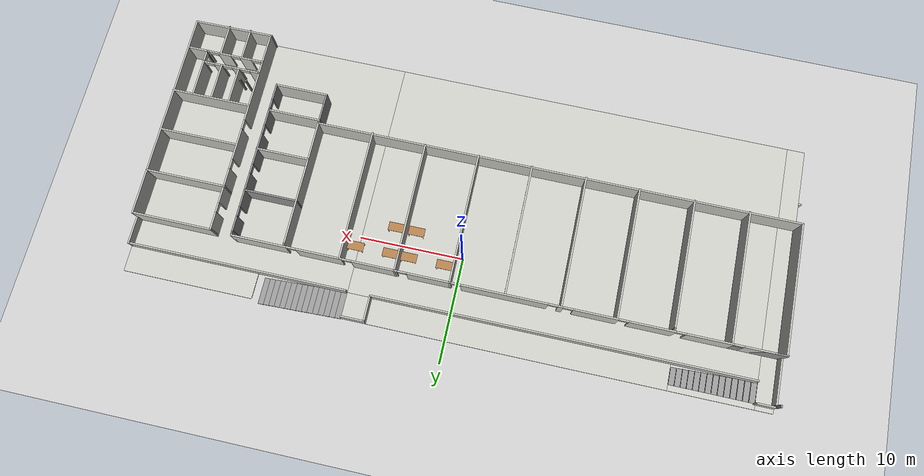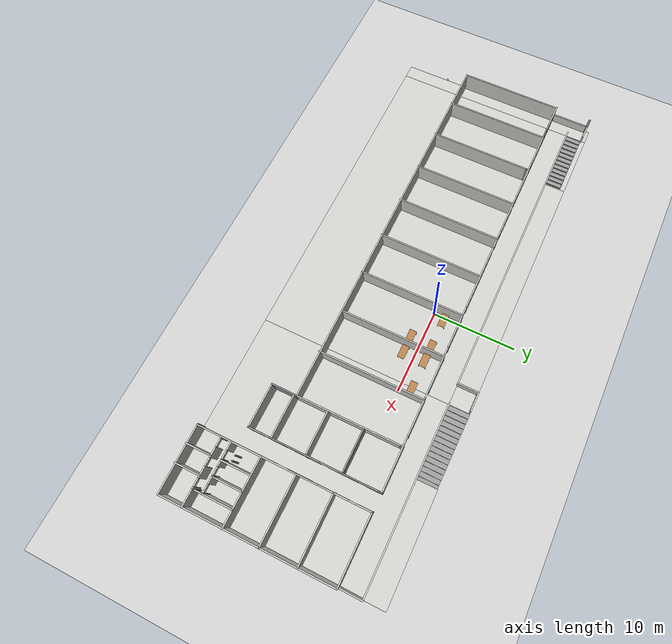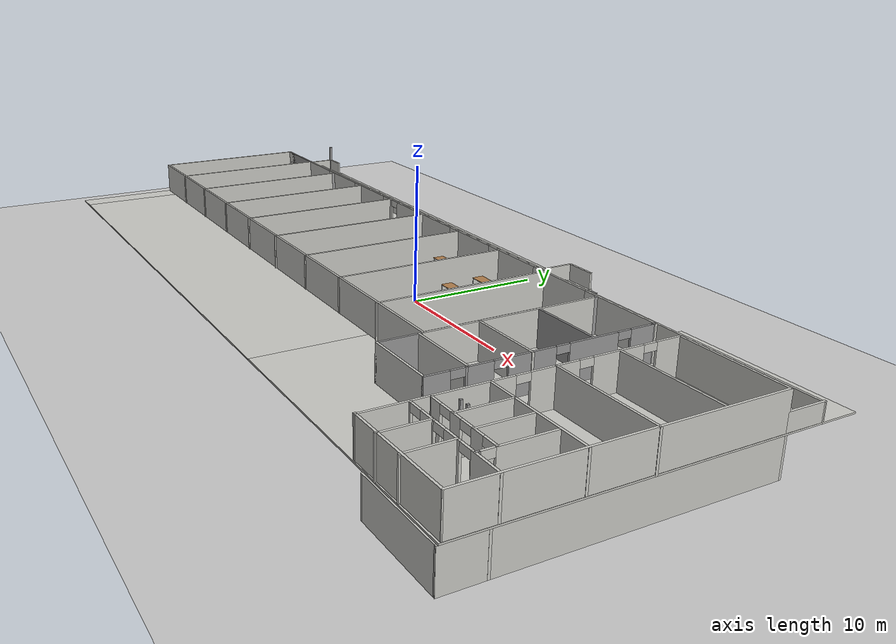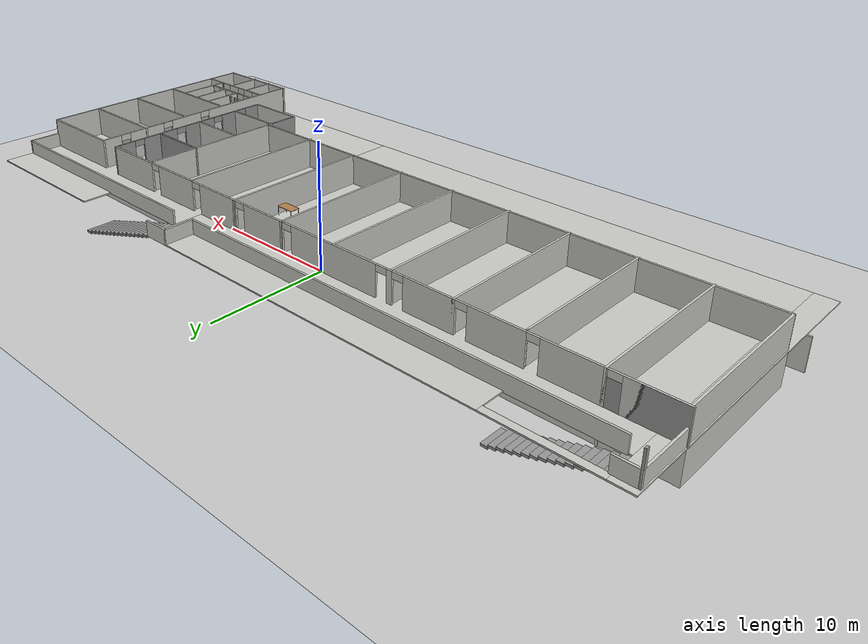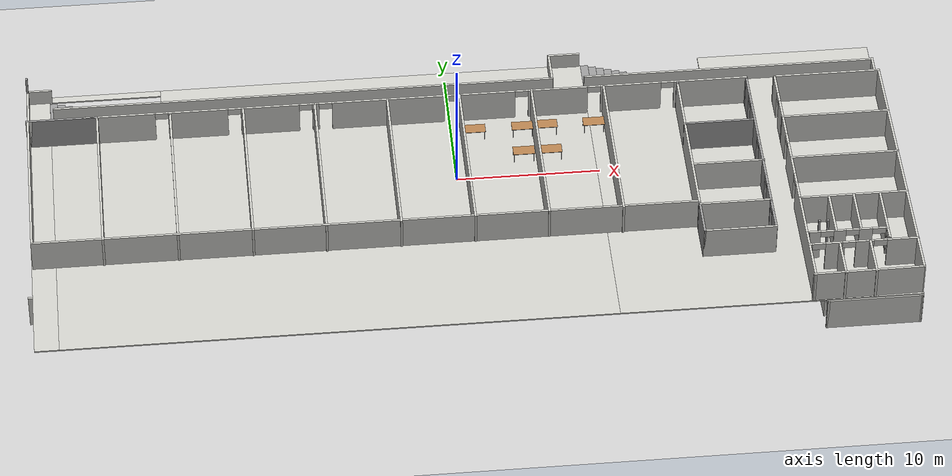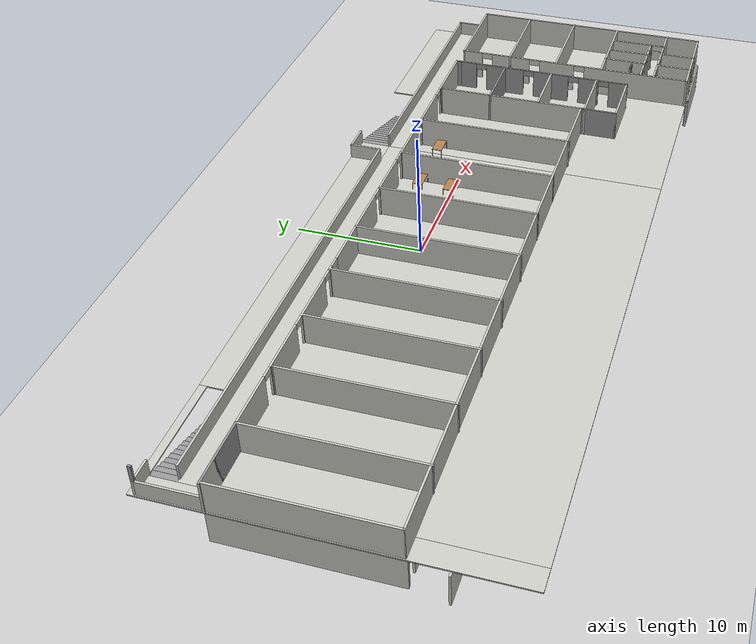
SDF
<sdf version="1.6">
 <world name="default">
  <light name="sun" type="directional">
   <pose>0 0 10 0 -0 0</pose>
   <diffuse>0.8 0.8 0.8 1</diffuse>
   <specular>0.2 0.2 0.2 1</specular>
   <attenuation>
    <range>1000</range>
    <constant>0.9</constant>
    <linear>0.01</linear>
    <quadratic>0.001</quadratic>
   </attenuation>
   <direction>-0.5 0.1 -0.9</direction>
  </light>
  <model name="ground_plane">
   <static>1</static>
   <link name="link">
    <collision name="collision">
     <geometry><plane><normal>0 0 1</normal><size>100 100</size></plane></geometry>
     <surface>
      <contact><collide_bitmask>65535</collide_bitmask></contact>
      <friction><ode><mu>100</mu><mu2>50</mu2></ode></friction>
     </surface>
    </collision>
    <visual name="visual">
     <cast_shadows>0</cast_shadows>
     <geometry><plane><normal>0 0 1</normal><size>100 100</size></plane></geometry>
     <material>
      <script><uri>file://media/materials/scripts/gazebo.material</uri><name>Gazebo/Grey</name></script>
     </material>
    </visual>
   </link>
  </model>
  <physics name="default_physics" default="0" type="ode">
   <real_time_update_rate>1000</real_time_update_rate>
   <max_step_size>0.001</max_step_size>
   <real_time_factor>1</real_time_factor>
   <ode>
    <solver>
     <type>quick</type>
     <iters>150</iters>
     <precon_iters>0</precon_iters>
     <sor>1.4</sor>
     <use_dynamic_moi_rescaling>1</use_dynamic_moi_rescaling>
    </solver>
    <constraints>
     <cfm>1e-05</cfm>
     <erp>0.2</erp>
     <contact_max_correcting_vel>2000</contact_max_correcting_vel>
     <contact_surface_layer>0.01</contact_surface_layer>
    </constraints>
   </ode>
  </physics>
  <scene><ambient>0.4 0.4 0.4 1</ambient><background>0.7 0.7 0.7 1</background><shadows>1</shadows></scene>
  <model name="ifes_bloco_m">
   <pose>0.003818 -4.2564 0 0 -0 0</pose>
   <link name="Floor_0">
    <pose>0.157128 0.038162 2.5 0 -0 0</pose>
    <visual name="Floor_0_Visual_0">
     <pose>-28.976 0 0.05 0 -0 0</pose>
     <geometry><box><size>1.64864 24.7557 0.1</size></box></geometry>
     <material>
      <script><uri>file://media/materials/scripts/gazebo.material</uri><name>Gazebo/CeilingTiled</name></script>
      <ambient>1 1 1 1</ambient>
     </material>
     <meta><layer>1</layer></meta>
    </visual>
    <collision name="Floor_0_Collision_0">
     <geometry><box><size>1.64864 24.7557 0.1</size></box></geometry>
     <pose>-28.976 0 0.05 0 -0 0</pose>
    </collision>
    <visual name="Floor_0_Visual_1">
     <pose>-9.42841 -1.21298 0.05 0 -0 0</pose>
     <geometry><box><size>37.4466 22.3297 0.1</size></box></geometry>
     <material>
      <script><uri>file://media/materials/scripts/gazebo.material</uri><name>Gazebo/CeilingTiled</name></script>
      <ambient>1 1 1 1</ambient>
     </material>
     <meta><layer>1</layer></meta>
    </visual>
    <collision name="Floor_0_Collision_1">
     <geometry><box><size>37.4466 22.3297 0.1</size></box></geometry>
     <pose>-9.42841 -1.21298 0.05 0 -0 0</pose>
    </collision>
    <visual name="Floor_0_Visual_2">
     <pose>19.5476 -1.22768 0.05 0 -0 0</pose>
     <geometry><box><size>20.5055 22.3003 0.1</size></box></geometry>
     <material>
      <script><uri>file://media/materials/scripts/gazebo.material</uri><name>Gazebo/CeilingTiled</name></script>
      <ambient>1 1 1 1</ambient>
     </material>
     <meta><layer>1</layer></meta>
    </visual>
    <collision name="Floor_0_Collision_2">
     <geometry><box><size>20.5055 22.3003 0.1</size></box></geometry>
     <pose>19.5476 -1.22768 0.05 0 -0 0</pose>
    </collision>
    <visual name="Floor_0_Visual_3">
     <pose>23.7241 11.1502 0.05 0 -0 0</pose>
     <geometry><box><size>12.1525 2.45536 0.1</size></box></geometry>
     <material>
      <script><uri>file://media/materials/scripts/gazebo.material</uri><name>Gazebo/CeilingTiled</name></script>
      <ambient>1 1 1 1</ambient>
     </material>
     <meta><layer>1</layer></meta>
    </visual>
    <collision name="Floor_0_Collision_3">
     <geometry><box><size>12.1525 2.45536 0.1</size></box></geometry>
     <pose>23.7241 11.1502 0.05 0 -0 0</pose>
    </collision>
    <visual name="Floor_0_Visual_4">
     <pose>-5.55039 11.1649 0.05 0 -0 0</pose>
     <geometry><box><size>29.6905 2.42596 0.1</size></box></geometry>
     <material>
      <script><uri>file://media/materials/scripts/gazebo.material</uri><name>Gazebo/CeilingTiled</name></script>
      <ambient>1 1 1 1</ambient>
     </material>
     <meta><layer>1</layer></meta>
    </visual>
    <collision name="Floor_0_Collision_4">
     <geometry><box><size>29.6905 2.42596 0.1</size></box></geometry>
     <pose>-5.55039 11.1649 0.05 0 -0 0</pose>
    </collision>
    <visual name="Floor_0_Visual_5">
     <pose>-24.2737 12.1043 0.05 0 -0 0</pose>
     <geometry><box><size>7.75603 0.546998 0.1</size></box></geometry>
     <material>
      <script><uri>file://media/materials/scripts/gazebo.material</uri><name>Gazebo/CeilingTiled</name></script>
      <ambient>1 1 1 1</ambient>
     </material>
     <meta><layer>1</layer></meta>
    </visual>
    <collision name="Floor_0_Collision_5">
     <geometry><box><size>7.75603 0.546998 0.1</size></box></geometry>
     <pose>-24.2737 12.1043 0.05 0 -0 0</pose>
    </collision>
   </link>
   <link name="Stairs_0">
    <visual name="Stairs_0_Visual_0">
     <pose>-20.4971 10.9295 0.083333 0 -0 -1.5708</pose>
     <geometry><box><size>1.87896 0.517069 0.166667</size></box></geometry>
     <material>
      <script><uri>file://media/materials/scripts/gazebo.material</uri><name>Gazebo/Grey</name></script>
      <ambient>1 1 1 1</ambient>
     </material>
     <meta><layer>0</layer></meta>
    </visual>
    <collision name="Stairs_0_Collision_0">
     <geometry><box><size>1.87896 0.517069 0.166667</size></box></geometry>
     <pose>-20.4971 10.9295 0.083333 0 -0 -1.5708</pose>
    </collision>
    <visual name="Stairs_0_Visual_1">
     <pose>-21.0141 10.9295 0.25 0 -0 -1.5708</pose>
     <geometry><box><size>1.87896 0.517069 0.166667</size></box></geometry>
     <material>
      <script><uri>file://media/materials/scripts/gazebo.material</uri><name>Gazebo/Grey</name></script>
      <ambient>1 1 1 1</ambient>
     </material>
     <meta><layer>0</layer></meta>
    </visual>
    <collision name="Stairs_0_Collision_1">
     <geometry><box><size>1.87896 0.517069 0.166667</size></box></geometry>
     <pose>-21.0141 10.9295 0.25 0 -0 -1.5708</pose>
    </collision>
    <visual name="Stairs_0_Visual_2">
     <pose>-21.5312 10.9295 0.416667 0 -0 -1.5708</pose>
     <geometry><box><size>1.87896 0.517069 0.166667</size></box></geometry>
     <material>
      <script><uri>file://media/materials/scripts/gazebo.material</uri><name>Gazebo/Grey</name></script>
      <ambient>1 1 1 1</ambient>
     </material>
     <meta><layer>0</layer></meta>
    </visual>
    <collision name="Stairs_0_Collision_2">
     <geometry><box><size>1.87896 0.517069 0.166667</size></box></geometry>
     <pose>-21.5312 10.9295 0.416667 0 -0 -1.5708</pose>
    </collision>
    <visual name="Stairs_0_Visual_3">
     <pose>-22.0483 10.9295 0.583333 0 -0 -1.5708</pose>
     <geometry><box><size>1.87896 0.517069 0.166667</size></box></geometry>
     <material>
      <script><uri>file://media/materials/scripts/gazebo.material</uri><name>Gazebo/Grey</name></script>
      <ambient>1 1 1 1</ambient>
     </material>
     <meta><layer>0</layer></meta>
    </visual>
    <collision name="Stairs_0_Collision_3">
     <geometry><box><size>1.87896 0.517069 0.166667</size></box></geometry>
     <pose>-22.0483 10.9295 0.583333 0 -0 -1.5708</pose>
    </collision>
    <visual name="Stairs_0_Visual_4">
     <pose>-22.5653 10.9295 0.75 0 -0 -1.5708</pose>
     <geometry><box><size>1.87896 0.517069 0.166667</size></box></geometry>
     <material>
      <script><uri>file://media/materials/scripts/gazebo.material</uri><name>Gazebo/Grey</name></script>
      <ambient>1 1 1 1</ambient>
     </material>
     <meta><layer>0</layer></meta>
    </visual>
    <collision name="Stairs_0_Collision_4">
     <geometry><box><size>1.87896 0.517069 0.166667</size></box></geometry>
     <pose>-22.5653 10.9295 0.75 0 -0 -1.5708</pose>
    </collision>
    <visual name="Stairs_0_Visual_5">
     <pose>-23.0824 10.9295 0.916667 0 -0 -1.5708</pose>
     <geometry><box><size>1.87896 0.517069 0.166667</size></box></geometry>
     <material>
      <script><uri>file://media/materials/scripts/gazebo.material</uri><name>Gazebo/Grey</name></script>
      <ambient>1 1 1 1</ambient>
     </material>
     <meta><layer>0</layer></meta>
    </visual>
    <collision name="Stairs_0_Collision_5">
     <geometry><box><size>1.87896 0.517069 0.166667</size></box></geometry>
     <pose>-23.0824 10.9295 0.916667 0 -0 -1.5708</pose>
    </collision>
    <visual name="Stairs_0_Visual_6">
     <pose>-23.5995 10.9295 1.08333 0 -0 -1.5708</pose>
     <geometry><box><size>1.87896 0.517069 0.166667</size></box></geometry>
     <material>
      <script><uri>file://media/materials/scripts/gazebo.material</uri><name>Gazebo/Grey</name></script>
      <ambient>1 1 1 1</ambient>
     </material>
     <meta><layer>0</layer></meta>
    </visual>
    <collision name="Stairs_0_Collision_6">
     <geometry><box><size>1.87896 0.517069 0.166667</size></box></geometry>
     <pose>-23.5995 10.9295 1.08333 0 -0 -1.5708</pose>
    </collision>
    <visual name="Stairs_0_Visual_7">
     <pose>-24.1166 10.9295 1.25 0 -0 -1.5708</pose>
     <geometry><box><size>1.87896 0.517069 0.166667</size></box></geometry>
     <material>
      <script><uri>file://media/materials/scripts/gazebo.material</uri><name>Gazebo/Grey</name></script>
      <ambient>1 1 1 1</ambient>
     </material>
     <meta><layer>0</layer></meta>
    </visual>
    <collision name="Stairs_0_Collision_7">
     <geometry><box><size>1.87896 0.517069 0.166667</size></box></geometry>
     <pose>-24.1166 10.9295 1.25 0 -0 -1.5708</pose>
    </collision>
    <visual name="Stairs_0_Visual_8">
     <pose>-24.6336 10.9295 1.41667 0 -0 -1.5708</pose>
     <geometry><box><size>1.87896 0.517069 0.166667</size></box></geometry>
     <material>
      <script><uri>file://media/materials/scripts/gazebo.material</uri><name>Gazebo/Grey</name></script>
      <ambient>1 1 1 1</ambient>
     </material>
     <meta><layer>0</layer></meta>
    </visual>
    <collision name="Stairs_0_Collision_8">
     <geometry><box><size>1.87896 0.517069 0.166667</size></box></geometry>
     <pose>-24.6336 10.9295 1.41667 0 -0 -1.5708</pose>
    </collision>
    <visual name="Stairs_0_Visual_9">
     <pose>-25.1507 10.9295 1.58333 0 -0 -1.5708</pose>
     <geometry><box><size>1.87896 0.517069 0.166667</size></box></geometry>
     <material>
      <script><uri>file://media/materials/scripts/gazebo.material</uri><name>Gazebo/Grey</name></script>
      <ambient>1 1 1 1</ambient>
     </material>
     <meta><layer>0</layer></meta>
    </visual>
    <collision name="Stairs_0_Collision_9">
     <geometry><box><size>1.87896 0.517069 0.166667</size></box></geometry>
     <pose>-25.1507 10.9295 1.58333 0 -0 -1.5708</pose>
    </collision>
    <visual name="Stairs_0_Visual_10">
     <pose>-25.6678 10.9295 1.75 0 -0 -1.5708</pose>
     <geometry><box><size>1.87896 0.517069 0.166667</size></box></geometry>
     <material>
      <script><uri>file://media/materials/scripts/gazebo.material</uri><name>Gazebo/Grey</name></script>
      <ambient>1 1 1 1</ambient>
     </material>
     <meta><layer>0</layer></meta>
    </visual>
    <collision name="Stairs_0_Collision_10">
     <geometry><box><size>1.87896 0.517069 0.166667</size></box></geometry>
     <pose>-25.6678 10.9295 1.75 0 -0 -1.5708</pose>
    </collision>
    <visual name="Stairs_0_Visual_11">
     <pose>-26.1848 10.9295 1.91667 0 -0 -1.5708</pose>
     <geometry><box><size>1.87896 0.517069 0.166667</size></box></geometry>
     <material>
      <script><uri>file://media/materials/scripts/gazebo.material</uri><name>Gazebo/Grey</name></script>
      <ambient>1 1 1 1</ambient>
     </material>
     <meta><layer>0</layer></meta>
    </visual>
    <collision name="Stairs_0_Collision_11">
     <geometry><box><size>1.87896 0.517069 0.166667</size></box></geometry>
     <pose>-26.1848 10.9295 1.91667 0 -0 -1.5708</pose>
    </collision>
    <visual name="Stairs_0_Visual_12">
     <pose>-26.7019 10.9295 2.08333 0 -0 -1.5708</pose>
     <geometry><box><size>1.87896 0.517069 0.166667</size></box></geometry>
     <material>
      <script><uri>file://media/materials/scripts/gazebo.material</uri><name>Gazebo/Grey</name></script>
      <ambient>1 1 1 1</ambient>
     </material>
     <meta><layer>0</layer></meta>
    </visual>
    <collision name="Stairs_0_Collision_12">
     <geometry><box><size>1.87896 0.517069 0.166667</size></box></geometry>
     <pose>-26.7019 10.9295 2.08333 0 -0 -1.5708</pose>
    </collision>
    <visual name="Stairs_0_Visual_13">
     <pose>-27.219 10.9295 2.25 0 -0 -1.5708</pose>
     <geometry><box><size>1.87896 0.517069 0.166667</size></box></geometry>
     <material>
      <script><uri>file://media/materials/scripts/gazebo.material</uri><name>Gazebo/Grey</name></script>
      <ambient>1 1 1 1</ambient>
     </material>
     <meta><layer>0</layer></meta>
    </visual>
    <collision name="Stairs_0_Collision_13">
     <geometry><box><size>1.87896 0.517069 0.166667</size></box></geometry>
     <pose>-27.219 10.9295 2.25 0 -0 -1.5708</pose>
    </collision>
    <visual name="Stairs_0_Visual_14">
     <pose>-27.736 10.9295 2.41667 0 -0 -1.5708</pose>
     <geometry><box><size>1.87896 0.517069 0.166667</size></box></geometry>
     <material>
      <script><uri>file://media/materials/scripts/gazebo.material</uri><name>Gazebo/Grey</name></script>
      <ambient>1 1 1 1</ambient>
     </material>
     <meta><layer>0</layer></meta>
    </visual>
    <collision name="Stairs_0_Collision_14">
     <geometry><box><size>1.87896 0.517069 0.166667</size></box></geometry>
     <pose>-27.736 10.9295 2.41667 0 -0 -1.5708</pose>
    </collision>
   </link>
   <link name="Stairs_1">
    <visual name="Stairs_1_Visual_0">
     <pose>17.5266 11.2024 0.083333 0 -0 -1.5708</pose>
     <geometry><box><size>2.4835 0.556867 0.166667</size></box></geometry>
     <material>
      <script><uri>file://media/materials/scripts/gazebo.material</uri><name>Gazebo/Grey</name></script>
      <ambient>1 1 1 1</ambient>
     </material>
     <meta><layer>0</layer></meta>
    </visual>
    <collision name="Stairs_1_Collision_0">
     <geometry><box><size>2.4835 0.556867 0.166667</size></box></geometry>
     <pose>17.5266 11.2024 0.083333 0 -0 -1.5708</pose>
    </collision>
    <visual name="Stairs_1_Visual_1">
     <pose>16.9697 11.2024 0.25 0 -0 -1.5708</pose>
     <geometry><box><size>2.4835 0.556867 0.166667</size></box></geometry>
     <material>
      <script><uri>file://media/materials/scripts/gazebo.material</uri><name>Gazebo/Grey</name></script>
      <ambient>1 1 1 1</ambient>
     </material>
     <meta><layer>0</layer></meta>
    </visual>
    <collision name="Stairs_1_Collision_1">
     <geometry><box><size>2.4835 0.556867 0.166667</size></box></geometry>
     <pose>16.9697 11.2024 0.25 0 -0 -1.5708</pose>
    </collision>
    <visual name="Stairs_1_Visual_2">
     <pose>16.4128 11.2024 0.416667 0 -0 -1.5708</pose>
     <geometry><box><size>2.4835 0.556867 0.166667</size></box></geometry>
     <material>
      <script><uri>file://media/materials/scripts/gazebo.material</uri><name>Gazebo/Grey</name></script>
      <ambient>1 1 1 1</ambient>
     </material>
     <meta><layer>0</layer></meta>
    </visual>
    <collision name="Stairs_1_Collision_2">
     <geometry><box><size>2.4835 0.556867 0.166667</size></box></geometry>
     <pose>16.4128 11.2024 0.416667 0 -0 -1.5708</pose>
    </collision>
    <visual name="Stairs_1_Visual_3">
     <pose>15.856 11.2024 0.583333 0 -0 -1.5708</pose>
     <geometry><box><size>2.4835 0.556867 0.166667</size></box></geometry>
     <material>
      <script><uri>file://media/materials/scripts/gazebo.material</uri><name>Gazebo/Grey</name></script>
      <ambient>1 1 1 1</ambient>
     </material>
     <meta><layer>0</layer></meta>
    </visual>
    <collision name="Stairs_1_Collision_3">
     <geometry><box><size>2.4835 0.556867 0.166667</size></box></geometry>
     <pose>15.856 11.2024 0.583333 0 -0 -1.5708</pose>
    </collision>
    <visual name="Stairs_1_Visual_4">
     <pose>15.2991 11.2024 0.75 0 -0 -1.5708</pose>
     <geometry><box><size>2.4835 0.556867 0.166667</size></box></geometry>
     <material>
      <script><uri>file://media/materials/scripts/gazebo.material</uri><name>Gazebo/Grey</name></script>
      <ambient>1 1 1 1</ambient>
     </material>
     <meta><layer>0</layer></meta>
    </visual>
    <collision name="Stairs_1_Collision_4">
     <geometry><box><size>2.4835 0.556867 0.166667</size></box></geometry>
     <pose>15.2991 11.2024 0.75 0 -0 -1.5708</pose>
    </collision>
    <visual name="Stairs_1_Visual_5">
     <pose>14.7422 11.2024 0.916667 0 -0 -1.5708</pose>
     <geometry><box><size>2.4835 0.556867 0.166667</size></box></geometry>
     <material>
      <script><uri>file://media/materials/scripts/gazebo.material</uri><name>Gazebo/Grey</name></script>
      <ambient>1 1 1 1</ambient>
     </material>
     <meta><layer>0</layer></meta>
    </visual>
    <collision name="Stairs_1_Collision_5">
     <geometry><box><size>2.4835 0.556867 0.166667</size></box></geometry>
     <pose>14.7422 11.2024 0.916667 0 -0 -1.5708</pose>
    </collision>
    <visual name="Stairs_1_Visual_6">
     <pose>14.1854 11.2024 1.08333 0 -0 -1.5708</pose>
     <geometry><box><size>2.4835 0.556867 0.166667</size></box></geometry>
     <material>
      <script><uri>file://media/materials/scripts/gazebo.material</uri><name>Gazebo/Grey</name></script>
      <ambient>1 1 1 1</ambient>
     </material>
     <meta><layer>0</layer></meta>
    </visual>
    <collision name="Stairs_1_Collision_6">
     <geometry><box><size>2.4835 0.556867 0.166667</size></box></geometry>
     <pose>14.1854 11.2024 1.08333 0 -0 -1.5708</pose>
    </collision>
    <visual name="Stairs_1_Visual_7">
     <pose>13.6285 11.2024 1.25 0 -0 -1.5708</pose>
     <geometry><box><size>2.4835 0.556867 0.166667</size></box></geometry>
     <material>
      <script><uri>file://media/materials/scripts/gazebo.material</uri><name>Gazebo/Grey</name></script>
      <ambient>1 1 1 1</ambient>
     </material>
     <meta><layer>0</layer></meta>
    </visual>
    <collision name="Stairs_1_Collision_7">
     <geometry><box><size>2.4835 0.556867 0.166667</size></box></geometry>
     <pose>13.6285 11.2024 1.25 0 -0 -1.5708</pose>
    </collision>
    <visual name="Stairs_1_Visual_8">
     <pose>13.0716 11.2024 1.41667 0 -0 -1.5708</pose>
     <geometry><box><size>2.4835 0.556867 0.166667</size></box></geometry>
     <material>
      <script><uri>file://media/materials/scripts/gazebo.material</uri><name>Gazebo/Grey</name></script>
      <ambient>1 1 1 1</ambient>
     </material>
     <meta><layer>0</layer></meta>
    </visual>
    <collision name="Stairs_1_Collision_8">
     <geometry><box><size>2.4835 0.556867 0.166667</size></box></geometry>
     <pose>13.0716 11.2024 1.41667 0 -0 -1.5708</pose>
    </collision>
    <visual name="Stairs_1_Visual_9">
     <pose>12.5148 11.2024 1.58333 0 -0 -1.5708</pose>
     <geometry><box><size>2.4835 0.556867 0.166667</size></box></geometry>
     <material>
      <script><uri>file://media/materials/scripts/gazebo.material</uri><name>Gazebo/Grey</name></script>
      <ambient>1 1 1 1</ambient>
     </material>
     <meta><layer>0</layer></meta>
    </visual>
    <collision name="Stairs_1_Collision_9">
     <geometry><box><size>2.4835 0.556867 0.166667</size></box></geometry>
     <pose>12.5148 11.2024 1.58333 0 -0 -1.5708</pose>
    </collision>
    <visual name="Stairs_1_Visual_10">
     <pose>11.9579 11.2024 1.75 0 -0 -1.5708</pose>
     <geometry><box><size>2.4835 0.556867 0.166667</size></box></geometry>
     <material>
      <script><uri>file://media/materials/scripts/gazebo.material</uri><name>Gazebo/Grey</name></script>
      <ambient>1 1 1 1</ambient>
     </material>
     <meta><layer>0</layer></meta>
    </visual>
    <collision name="Stairs_1_Collision_10">
     <geometry><box><size>2.4835 0.556867 0.166667</size></box></geometry>
     <pose>11.9579 11.2024 1.75 0 -0 -1.5708</pose>
    </collision>
    <visual name="Stairs_1_Visual_11">
     <pose>11.401 11.2024 1.91667 0 -0 -1.5708</pose>
     <geometry><box><size>2.4835 0.556867 0.166667</size></box></geometry>
     <material>
      <script><uri>file://media/materials/scripts/gazebo.material</uri><name>Gazebo/Grey</name></script>
      <ambient>1 1 1 1</ambient>
     </material>
     <meta><layer>0</layer></meta>
    </visual>
    <collision name="Stairs_1_Collision_11">
     <geometry><box><size>2.4835 0.556867 0.166667</size></box></geometry>
     <pose>11.401 11.2024 1.91667 0 -0 -1.5708</pose>
    </collision>
    <visual name="Stairs_1_Visual_12">
     <pose>10.8442 11.2024 2.08333 0 -0 -1.5708</pose>
     <geometry><box><size>2.4835 0.556867 0.166667</size></box></geometry>
     <material>
      <script><uri>file://media/materials/scripts/gazebo.material</uri><name>Gazebo/Grey</name></script>
      <ambient>1 1 1 1</ambient>
     </material>
     <meta><layer>0</layer></meta>
    </visual>
    <collision name="Stairs_1_Collision_12">
     <geometry><box><size>2.4835 0.556867 0.166667</size></box></geometry>
     <pose>10.8442 11.2024 2.08333 0 -0 -1.5708</pose>
    </collision>
    <visual name="Stairs_1_Visual_13">
     <pose>10.2873 11.2024 2.25 0 -0 -1.5708</pose>
     <geometry><box><size>2.4835 0.556867 0.166667</size></box></geometry>
     <material>
      <script><uri>file://media/materials/scripts/gazebo.material</uri><name>Gazebo/Grey</name></script>
      <ambient>1 1 1 1</ambient>
     </material>
     <meta><layer>0</layer></meta>
    </visual>
    <collision name="Stairs_1_Collision_13">
     <geometry><box><size>2.4835 0.556867 0.166667</size></box></geometry>
     <pose>10.2873 11.2024 2.25 0 -0 -1.5708</pose>
    </collision>
    <visual name="Stairs_1_Visual_14">
     <pose>9.73044 11.2024 2.41667 0 -0 -1.5708</pose>
     <geometry><box><size>2.4835 0.556867 0.166667</size></box></geometry>
     <material>
      <script><uri>file://media/materials/scripts/gazebo.material</uri><name>Gazebo/Grey</name></script>
      <ambient>1 1 1 1</ambient>
     </material>
     <meta><layer>0</layer></meta>
    </visual>
    <collision name="Stairs_1_Collision_14">
     <geometry><box><size>2.4835 0.556867 0.166667</size></box></geometry>
     <pose>9.73044 11.2024 2.41667 0 -0 -1.5708</pose>
    </collision>
   </link>
   <link name="Wall_0">
    <collision name="Wall_0_Collision">
     <geometry><box><size>59.5 0.15 2.5</size></box></geometry>
     <pose>0 0 1.25 0 -0 0</pose>
    </collision>
    <visual name="Wall_0_Visual">
     <pose>0 0 1.25 0 -0 0</pose>
     <geometry><box><size>59.5 0.15 2.5</size></box></geometry>
     <material>
      <script><uri>file://media/materials/scripts/gazebo.material</uri><name>Gazebo/CeilingTiled</name></script>
      <ambient>1 1 1 1</ambient>
     </material>
     <meta><layer>0</layer></meta>
    </visual>
    <pose>0.181948 7.4609 0 0 -0 0</pose>
   </link>
   <link name="Wall_1">
    <collision name="Wall_1_Collision">
     <geometry><box><size>19.98 0.15 2.5</size></box></geometry>
     <pose>0 0 1.25 0 -0 0</pose>
    </collision>
    <visual name="Wall_1_Visual">
     <pose>0 0 1.25 0 -0 0</pose>
     <geometry><box><size>19.98 0.15 2.5</size></box></geometry>
     <material>
      <script><uri>file://media/materials/scripts/gazebo.material</uri><name>Gazebo/CeilingTiled</name></script>
      <ambient>1 1 1 1</ambient>
     </material>
     <meta><layer>0</layer></meta>
    </visual>
    <pose>29.8619 -2.4541 0 0 -0 -1.57029</pose>
   </link>
   <link name="Wall_10">
    <collision name="Wall_10_Collision">
     <geometry><box><size>6.25 0.15 2.5</size></box></geometry>
     <pose>0 0 1.25 0 -0 0</pose>
    </collision>
    <visual name="Wall_10_Visual">
     <pose>0 0 1.25 0 -0 0</pose>
     <geometry><box><size>6.25 0.15 2.5</size></box></geometry>
     <material>
      <script><uri>file://media/materials/scripts/gazebo.material</uri><name>Gazebo/CeilingTiled</name></script>
      <ambient>1 1 1 1</ambient>
     </material>
     <meta><layer>0</layer></meta>
    </visual>
    <pose>26.7153 -7.31464 0 0 -0 3.14159</pose>
   </link>
   <link name="Wall_101">
    <collision name="Wall_101_Collision">
     <geometry><box><size>5 0.15 2.5</size></box></geometry>
     <pose>0 0 1.25 0 -0 0</pose>
    </collision>
    <visual name="Wall_101_Visual">
     <pose>0 0 1.25 0 -0 0</pose>
     <geometry><box><size>5 0.15 2.5</size></box></geometry>
     <material>
      <script><uri>file://media/materials/scripts/gazebo.material</uri><name>Gazebo/CeilingTiled</name></script>
      <ambient>1 1 1 1</ambient>
     </material>
     <meta><layer>1</layer></meta>
    </visual>
    <pose>18.1581 -0.902525 2.5 0 -0 3.14159</pose>
   </link>
   <link name="Wall_104">
    <collision name="Wall_104_Collision">
     <geometry><box><size>4.54023 0.15 1.25</size></box></geometry>
     <pose>0 0 0.625 0 -0 0</pose>
    </collision>
    <visual name="Wall_104_Visual">
     <pose>0 0 0.625 0 -0 0</pose>
     <geometry><box><size>4.54023 0.15 1.25</size></box></geometry>
     <material>
      <script><uri>file://media/materials/scripts/gazebo.material</uri><name>Gazebo/CeilingTiled</name></script>
      <ambient>0.921569 0.807843 0.615686 1</ambient>
     </material>
     <meta><layer>1</layer></meta>
    </visual>
    <pose>-29.4926 9.61614 2.5 0 -0 1.5708</pose>
   </link>
   <link name="Wall_105">
    <collision name="Wall_105_Collision">
     <geometry><box><size>0.25 0.15 2.5</size></box></geometry>
     <pose>0 0 1.25 0 -0 0</pose>
    </collision>
    <visual name="Wall_105_Visual">
     <pose>0 0 1.25 0 -0 0</pose>
     <geometry><box><size>0.25 0.15 2.5</size></box></geometry>
     <material>
      <script><uri>file://media/materials/scripts/gazebo.material</uri><name>Gazebo/Grey</name></script>
      <ambient>1 1 1 1</ambient>
     </material>
     <meta><layer>1</layer></meta>
    </visual>
    <pose>-29.4926 11.8611 2.5 0 -0 1.5708</pose>
   </link>
   <link name="Wall_106">
    <collision name="Wall_106_Collision">
     <geometry><box><size>1.75 0.15 1.25</size></box></geometry>
     <pose>0 0 0.625 0 -0 0</pose>
    </collision>
    <visual name="Wall_106_Visual">
     <pose>0 0 0.625 0 -0 0</pose>
     <geometry><box><size>1.75 0.15 1.25</size></box></geometry>
     <material>
      <script><uri>file://media/materials/scripts/gazebo.material</uri><name>Gazebo/CeilingTiled</name></script>
      <ambient>0.921569 0.807843 0.615686 1</ambient>
     </material>
     <meta><layer>1</layer></meta>
    </visual>
    <pose>-28.6927 11.9111 2.5 0 -0 0</pose>
   </link>
   <link name="Wall_108">
    <collision name="Wall_108_Collision">
     <geometry><box><size>35 0.15 1.25</size></box></geometry>
     <pose>0 0 0.625 0 -0 0</pose>
    </collision>
    <visual name="Wall_108_Visual">
     <pose>0 0 0.625 0 -0 0</pose>
     <geometry><box><size>35 0.15 1.25</size></box></geometry>
     <material>
      <script><uri>file://media/materials/scripts/gazebo.material</uri><name>Gazebo/CeilingTiled</name></script>
      <ambient>0.921569 0.807843 0.615686 1</ambient>
     </material>
     <meta><layer>1</layer></meta>
    </visual>
    <pose>-10.2627 9.98214 2.5 0 -0 0</pose>
   </link>
   <link name="Wall_110">
    <collision name="Wall_110_Collision">
     <geometry><box><size>2.5 0.15 1.25</size></box></geometry>
     <pose>0 0 0.625 0 -0 0</pose>
    </collision>
    <visual name="Wall_110_Visual">
     <pose>0 0 0.625 0 -0 0</pose>
     <geometry><box><size>2.5 0.15 1.25</size></box></geometry>
     <material>
      <script><uri>file://media/materials/scripts/gazebo.material</uri><name>Gazebo/CeilingTiled</name></script>
      <ambient>0.921569 0.807843 0.615686 1</ambient>
     </material>
     <meta><layer>1</layer></meta>
    </visual>
    <pose>7.19935 11.1661 2.5 0 -0 1.5708</pose>
   </link>
   <link name="Wall_111">
    <collision name="Wall_111_Collision">
     <geometry><box><size>2.25 0.15 1.25</size></box></geometry>
     <pose>0 0 0.625 0 -0 0</pose>
    </collision>
    <visual name="Wall_111_Visual">
     <pose>0 0 0.625 0 -0 0</pose>
     <geometry><box><size>2.25 0.15 1.25</size></box></geometry>
     <material>
      <script><uri>file://media/materials/scripts/gazebo.material</uri><name>Gazebo/CeilingTiled</name></script>
      <ambient>0.921569 0.807843 0.615686 1</ambient>
     </material>
     <meta><layer>1</layer></meta>
    </visual>
    <pose>8.24935 12.3411 2.5 0 -0 0</pose>
   </link>
   <link name="Wall_115">
    <collision name="Wall_115_Collision">
     <geometry><box><size>20.5 0.15 1.2</size></box></geometry>
     <pose>0 0 0.6 0 -0 0</pose>
    </collision>
    <visual name="Wall_115_Visual">
     <pose>0 0 0.6 0 -0 0</pose>
     <geometry><box><size>20.5 0.15 1.2</size></box></geometry>
     <material>
      <script><uri>file://media/materials/scripts/gazebo.material</uri><name>Gazebo/CeilingTiled</name></script>
      <ambient>0.921569 0.807843 0.615686 1</ambient>
     </material>
     <meta><layer>1</layer></meta>
    </visual>
    <pose>19.7014 9.98264 2.5 0 -0 -0.000737</pose>
   </link>
   <link name="Wall_118">
    <collision name="Wall_118_Collision">
     <geometry><box><size>7.5 0.15 2.5</size></box></geometry>
     <pose>0 0 1.25 0 -0 0</pose>
    </collision>
    <visual name="Wall_118_Visual">
     <pose>0 0 1.25 0 -0 0</pose>
     <geometry><box><size>7.5 0.15 2.5</size></box></geometry>
     <material>
      <script><uri>file://media/materials/scripts/gazebo.material</uri><name>Gazebo/CeilingTiled</name></script>
      <ambient>1 1 1 1</ambient>
     </material>
     <meta><layer>1</layer></meta>
    </visual>
    <pose>26.1723 3.25797 2.5 0 -0 0</pose>
   </link>
   <link name="Wall_12">
    <collision name="Wall_12_Collision">
     <geometry><box><size>0.15 0.15 2.5</size></box></geometry>
     <pose>0 0 1.25 0 -0 0</pose>
    </collision>
    <visual name="Wall_12_Visual">
     <pose>0 0 1.25 0 -0 0</pose>
     <geometry><box><size>0.15 0.15 2.5</size></box></geometry>
     <material>
      <script><uri>file://media/materials/scripts/gazebo.material</uri><name>Gazebo/Grey</name></script>
      <ambient>1 1 1 1</ambient>
     </material>
     <meta><layer>0</layer></meta>
    </visual>
    <pose>23.6653 -7.31464 0 0 -0 0</pose>
   </link>
   <link name="Wall_120">
    <collision name="Wall_120_Collision">
     <geometry><box><size>7.5 0.15 2.5</size></box></geometry>
     <pose>0 0 1.25 0 -0 0</pose>
    </collision>
    <visual name="Wall_120_Visual">
     <pose>0 0 1.25 0 -0 0</pose>
     <geometry><box><size>7.5 0.15 2.5</size></box></geometry>
     <material>
      <script><uri>file://media/materials/scripts/gazebo.material</uri><name>Gazebo/CeilingTiled</name></script>
      <ambient>1 1 1 1</ambient>
     </material>
     <meta><layer>1</layer></meta>
    </visual>
    <pose>26.2075 -0.857943 2.5 0 -0 0</pose>
   </link>
   <link name="Wall_121">
    <collision name="Wall_121_Collision">
     <geometry><box><size>0.15 0.15 2.5</size></box></geometry>
     <pose>0 0 1.25 0 -0 0</pose>
    </collision>
    <visual name="Wall_121_Visual">
     <pose>0 0 1.25 0 -0 0</pose>
     <geometry><box><size>0.15 0.15 2.5</size></box></geometry>
     <material>
      <script><uri>file://media/materials/scripts/gazebo.material</uri><name>Gazebo/Grey</name></script>
      <ambient>1 1 1 1</ambient>
     </material>
     <meta><layer>1</layer></meta>
    </visual>
    <pose>29.8825 -0.857943 2.5 0 -0 0</pose>
   </link>
   <link name="Wall_124">
    <collision name="Wall_124_Collision">
     <geometry><box><size>7.5 0.15 2.5</size></box></geometry>
     <pose>0 0 1.25 0 -0 0</pose>
    </collision>
    <visual name="Wall_124_Visual">
     <pose>0 0 1.25 0 -0 0</pose>
     <geometry><box><size>7.5 0.15 2.5</size></box></geometry>
     <material>
      <script><uri>file://media/materials/scripts/gazebo.material</uri><name>Gazebo/CeilingTiled</name></script>
      <ambient>1 1 1 1</ambient>
     </material>
     <meta><layer>1</layer></meta>
    </visual>
    <pose>26.2012 -4.84441 2.5 0 -0 0</pose>
   </link>
   <link name="Wall_129">
    <collision name="Wall_129_Collision">
     <geometry><box><size>3.5 0.15 2.5</size></box></geometry>
     <pose>0 0 1.25 0 -0 0</pose>
    </collision>
    <visual name="Wall_129_Visual">
     <pose>0 0 1.25 0 -0 0</pose>
     <geometry><box><size>3.5 0.15 2.5</size></box></geometry>
     <material>
      <script><uri>file://media/materials/scripts/gazebo.material</uri><name>Gazebo/CeilingTiled</name></script>
      <ambient>1 1 1 1</ambient>
     </material>
     <meta><layer>1</layer></meta>
    </visual>
    <pose>24.5069 -6.54663 2.5 0 -0 -1.5708</pose>
   </link>
   <link name="Wall_131">
    <collision name="Wall_131_Collision">
     <geometry><box><size>3.5 0.15 2.5</size></box></geometry>
     <pose>0 0 1.25 0 -0 0</pose>
    </collision>
    <visual name="Wall_131_Visual">
     <pose>0 0 1.25 0 -0 0</pose>
     <geometry><box><size>3.5 0.15 2.5</size></box></geometry>
     <material>
      <script><uri>file://media/materials/scripts/gazebo.material</uri><name>Gazebo/CeilingTiled</name></script>
      <ambient>1 1 1 1</ambient>
     </material>
     <meta><layer>1</layer></meta>
    </visual>
    <pose>26.203 -6.54862 2.5 0 -0 -1.5708</pose>
   </link>
   <link name="Wall_133">
    <pose>28.0029 -7.04663 2.5 0 -0 -1.5708</pose>
    <visual name="Wall_133_Visual_0">
     <pose>-0.471414 0 1.25 0 -0 0</pose>
     <geometry><box><size>3.55717 0.15 2.5</size></box></geometry>
     <material>
      <script><uri>file://media/materials/scripts/gazebo.material</uri><name>Gazebo/CeilingTiled</name></script>
      <ambient>1 1 1 1</ambient>
     </material>
     <meta><layer>1</layer></meta>
    </visual>
    <collision name="Wall_133_Collision_0">
     <geometry><box><size>3.55717 0.15 2.5</size></box></geometry>
     <pose>-0.471414 0 1.25 0 -0 0</pose>
    </collision>
    <visual name="Wall_133_Visual_1">
     <pose>2.22859 0 1.25 0 -0 0</pose>
     <geometry><box><size>0.042828 0.15 2.5</size></box></geometry>
     <material>
      <script><uri>file://media/materials/scripts/gazebo.material</uri><name>Gazebo/CeilingTiled</name></script>
      <ambient>1 1 1 1</ambient>
     </material>
     <meta><layer>1</layer></meta>
    </visual>
    <collision name="Wall_133_Collision_1">
     <geometry><box><size>0.042828 0.15 2.5</size></box></geometry>
     <pose>2.22859 0 1.25 0 -0 0</pose>
    </collision>
    <visual name="Wall_133_Visual_2">
     <pose>1.75717 0 2.25 0 -0 0</pose>
     <geometry><box><size>0.9 0.15 0.5</size></box></geometry>
     <material>
      <script><uri>file://media/materials/scripts/gazebo.material</uri><name>Gazebo/CeilingTiled</name></script>
      <ambient>1 1 1 1</ambient>
     </material>
     <meta><layer>1</layer></meta>
    </visual>
    <collision name="Wall_133_Collision_2">
     <geometry><box><size>0.9 0.15 0.5</size></box></geometry>
     <pose>1.75717 0 2.25 0 -0 0</pose>
    </collision>
   </link>
   <link name="Wall_134">
    <collision name="Wall_134_Collision">
     <geometry><box><size>0.25 0.15 2.5</size></box></geometry>
     <pose>0 0 1.25 0 -0 0</pose>
    </collision>
    <visual name="Wall_134_Visual">
     <pose>0 0 1.25 0 -0 0</pose>
     <geometry><box><size>0.25 0.15 2.5</size></box></geometry>
     <material>
      <script><uri>file://media/materials/scripts/gazebo.material</uri><name>Gazebo/Grey</name></script>
      <ambient>1 1 1 1</ambient>
     </material>
     <meta><layer>1</layer></meta>
    </visual>
    <pose>28.0029 -9.27163 2.5 0 -0 -1.5708</pose>
   </link>
   <link name="Wall_136">
    <collision name="Wall_136_Collision">
     <geometry><box><size>3 0.15 2.5</size></box></geometry>
     <pose>0 0 1.25 0 -0 0</pose>
    </collision>
    <visual name="Wall_136_Visual">
     <pose>0 0 1.25 0 -0 0</pose>
     <geometry><box><size>3 0.15 2.5</size></box></geometry>
     <material>
      <script><uri>file://media/materials/scripts/gazebo.material</uri><name>Gazebo/CeilingTiled</name></script>
      <ambient>1 1 1 1</ambient>
     </material>
     <meta><layer>1</layer></meta>
    </visual>
    <pose>24.5584 -10.8398 2.5 0 -0 -1.5708</pose>
   </link>
   <link name="Wall_138">
    <collision name="Wall_138_Collision">
     <geometry><box><size>3 0.15 2.5</size></box></geometry>
     <pose>0 0 1.25 0 -0 0</pose>
    </collision>
    <visual name="Wall_138_Visual">
     <pose>0 0 1.25 0 -0 0</pose>
     <geometry><box><size>3 0.15 2.5</size></box></geometry>
     <material>
      <script><uri>file://media/materials/scripts/gazebo.material</uri><name>Gazebo/CeilingTiled</name></script>
      <ambient>1 1 1 1</ambient>
     </material>
     <meta><layer>1</layer></meta>
    </visual>
    <pose>26.6381 -10.8335 2.5 0 -0 -1.5708</pose>
   </link>
   <link name="Wall_14">
    <collision name="Wall_14_Collision">
     <geometry><box><size>6.5 0.15 2.5</size></box></geometry>
     <pose>0 0 1.25 0 -0 0</pose>
    </collision>
    <visual name="Wall_14_Visual">
     <pose>0 0 1.25 0 -0 0</pose>
     <geometry><box><size>6.5 0.15 2.5</size></box></geometry>
     <material>
      <script><uri>file://media/materials/scripts/gazebo.material</uri><name>Gazebo/CeilingTiled</name></script>
      <ambient>1 1 1 1</ambient>
     </material>
     <meta><layer>0</layer></meta>
    </visual>
    <pose>26.6942 -9.78365 0 0 -0 0</pose>
   </link>
   <link name="Wall_141">
    <collision name="Wall_141_Collision">
     <geometry><box><size>2.71955 0.15 1.25</size></box></geometry>
     <pose>0 0 0.625 0 -0 0</pose>
    </collision>
    <visual name="Wall_141_Visual">
     <pose>0 0 0.625 0 -0 0</pose>
     <geometry><box><size>2.71955 0.15 1.25</size></box></geometry>
     <material>
      <script><uri>file://media/materials/scripts/gazebo.material</uri><name>Gazebo/CeilingTiled</name></script>
      <ambient>0.921569 0.807843 0.615686 1</ambient>
     </material>
     <meta><layer>1</layer></meta>
    </visual>
    <pose>29.8668 8.69064 2.5 0 -0 -1.57819</pose>
   </link>
   <link name="Wall_144">
    <collision name="Wall_144_Collision">
     <geometry><box><size>7.50007 0.15 2.5</size></box></geometry>
     <pose>0 0 1.25 0 -0 0</pose>
    </collision>
    <visual name="Wall_144_Visual">
     <pose>0 0 1.25 0 -0 0</pose>
     <geometry><box><size>7.50007 0.15 2.5</size></box></geometry>
     <material>
      <script><uri>file://media/materials/scripts/gazebo.material</uri><name>Gazebo/CeilingTiled</name></script>
      <ambient>1 1 1 1</ambient>
     </material>
     <meta><layer>1</layer></meta>
    </visual>
    <pose>26.1821 7.41341 2.5 0 -0 3.13962</pose>
   </link>
   <link name="Wall_157">
    <collision name="Wall_157_Collision">
     <geometry><box><size>5 0.15 2.5</size></box></geometry>
     <pose>0 0 1.25 0 -0 0</pose>
    </collision>
    <visual name="Wall_157_Visual">
     <pose>0 0 1.25 0 -0 0</pose>
     <geometry><box><size>5 0.15 2.5</size></box></geometry>
     <material>
      <script><uri>file://media/materials/scripts/gazebo.material</uri><name>Gazebo/Grey</name></script>
      <ambient>1 1 1 1</ambient>
     </material>
     <meta><layer>1</layer></meta>
    </visual>
    <pose>-27.1432 7.51797 2.5 0 -0 3.14159</pose>
   </link>
   <link name="Wall_158">
    <pose>-4.51821 7.51797 2.5 0 -0 0</pose>
    <visual name="Wall_158_Visual_0">
     <pose>-23.1848 0 1.25 0 -0 0</pose>
     <geometry><box><size>3.88049 0.15 2.5</size></box></geometry>
     <material>
      <script><uri>file://media/materials/scripts/gazebo.material</uri><name>Gazebo/CeilingTiled</name></script>
      <ambient>1 1 1 1</ambient>
     </material>
     <meta><layer>1</layer></meta>
    </visual>
    <collision name="Wall_158_Collision_0">
     <geometry><box><size>3.88049 0.15 2.5</size></box></geometry>
     <pose>-23.1848 0 1.25 0 -0 0</pose>
    </collision>
    <visual name="Wall_158_Visual_1">
     <pose>-18.2616 0 1.25 0 -0 0</pose>
     <geometry><box><size>4.16574 0.15 2.5</size></box></geometry>
     <material>
      <script><uri>file://media/materials/scripts/gazebo.material</uri><name>Gazebo/CeilingTiled</name></script>
      <ambient>1 1 1 1</ambient>
     </material>
     <meta><layer>1</layer></meta>
    </visual>
    <collision name="Wall_158_Collision_1">
     <geometry><box><size>4.16574 0.15 2.5</size></box></geometry>
     <pose>-18.2616 0 1.25 0 -0 0</pose>
    </collision>
    <visual name="Wall_158_Visual_2">
     <pose>-13.2135 0 1.25 0 -0 0</pose>
     <geometry><box><size>4.13056 0.15 2.5</size></box></geometry>
     <material>
      <script><uri>file://media/materials/scripts/gazebo.material</uri><name>Gazebo/CeilingTiled</name></script>
      <ambient>1 1 1 1</ambient>
     </material>
     <meta><layer>1</layer></meta>
    </visual>
    <collision name="Wall_158_Collision_2">
     <geometry><box><size>4.13056 0.15 2.5</size></box></geometry>
     <pose>-13.2135 0 1.25 0 -0 0</pose>
    </collision>
    <visual name="Wall_158_Visual_3">
     <pose>-8.2181 0 1.25 0 -0 0</pose>
     <geometry><box><size>4.0602 0.15 2.5</size></box></geometry>
     <material>
      <script><uri>file://media/materials/scripts/gazebo.material</uri><name>Gazebo/CeilingTiled</name></script>
      <ambient>1 1 1 1</ambient>
     </material>
     <meta><layer>1</layer></meta>
    </visual>
    <collision name="Wall_158_Collision_3">
     <geometry><box><size>4.0602 0.15 2.5</size></box></geometry>
     <pose>-8.2181 0 1.25 0 -0 0</pose>
    </collision>
    <visual name="Wall_158_Visual_4">
     <pose>-5.05201 0 1.25 0 -0 0</pose>
     <geometry><box><size>0.471971 0.15 2.5</size></box></geometry>
     <material>
      <script><uri>file://media/materials/scripts/gazebo.material</uri><name>Gazebo/CeilingTiled</name></script>
      <ambient>1 1 1 1</ambient>
     </material>
     <meta><layer>1</layer></meta>
    </visual>
    <collision name="Wall_158_Collision_4">
     <geometry><box><size>0.471971 0.15 2.5</size></box></geometry>
     <pose>-5.05201 0 1.25 0 -0 0</pose>
    </collision>
    <visual name="Wall_158_Visual_5">
     <pose>-0.003861 0 1.25 0 -0 0</pose>
     <geometry><box><size>7.82433 0.15 2.5</size></box></geometry>
     <material>
      <script><uri>file://media/materials/scripts/gazebo.material</uri><name>Gazebo/CeilingTiled</name></script>
      <ambient>1 1 1 1</ambient>
     </material>
     <meta><layer>1</layer></meta>
    </visual>
    <collision name="Wall_158_Collision_5">
     <geometry><box><size>7.82433 0.15 2.5</size></box></geometry>
     <pose>-0.003861 0 1.25 0 -0 0</pose>
    </collision>
    <visual name="Wall_158_Visual_6">
     <pose>6.83841 0 1.25 0 -0 0</pose>
     <geometry><box><size>4.0602 0.15 2.5</size></box></geometry>
     <material>
      <script><uri>file://media/materials/scripts/gazebo.material</uri><name>Gazebo/CeilingTiled</name></script>
      <ambient>1 1 1 1</ambient>
     </material>
     <meta><layer>1</layer></meta>
    </visual>
    <collision name="Wall_158_Collision_6">
     <geometry><box><size>4.0602 0.15 2.5</size></box></geometry>
     <pose>6.83841 0 1.25 0 -0 0</pose>
    </collision>
    <visual name="Wall_158_Visual_7">
     <pose>11.8514 0 1.25 0 -0 0</pose>
     <geometry><box><size>4.16574 0.15 2.5</size></box></geometry>
     <material>
      <script><uri>file://media/materials/scripts/gazebo.material</uri><name>Gazebo/CeilingTiled</name></script>
      <ambient>1 1 1 1</ambient>
     </material>
     <meta><layer>1</layer></meta>
    </visual>
    <collision name="Wall_158_Collision_7">
     <geometry><box><size>4.16574 0.15 2.5</size></box></geometry>
     <pose>11.8514 0 1.25 0 -0 0</pose>
    </collision>
    <visual name="Wall_158_Visual_8">
     <pose>16.9523 0 1.25 0 -0 0</pose>
     <geometry><box><size>4.2361 0.15 2.5</size></box></geometry>
     <material>
      <script><uri>file://media/materials/scripts/gazebo.material</uri><name>Gazebo/CeilingTiled</name></script>
      <ambient>1 1 1 1</ambient>
     </material>
     <meta><layer>1</layer></meta>
    </visual>
    <collision name="Wall_158_Collision_8">
     <geometry><box><size>4.2361 0.15 2.5</size></box></geometry>
     <pose>16.9523 0 1.25 0 -0 0</pose>
    </collision>
    <visual name="Wall_158_Visual_9">
     <pose>22.5477 0 1.25 0 -0 0</pose>
     <geometry><box><size>5.15465 0.15 2.5</size></box></geometry>
     <material>
      <script><uri>file://media/materials/scripts/gazebo.material</uri><name>Gazebo/CeilingTiled</name></script>
      <ambient>1 1 1 1</ambient>
     </material>
     <meta><layer>1</layer></meta>
    </visual>
    <collision name="Wall_158_Collision_9">
     <geometry><box><size>5.15465 0.15 2.5</size></box></geometry>
     <pose>22.5477 0 1.25 0 -0 0</pose>
    </collision>
    <visual name="Wall_158_Visual_10">
     <pose>-20.7945 0 2.25 0 -0 0</pose>
     <geometry><box><size>0.9 0.15 0.5</size></box></geometry>
     <material>
      <script><uri>file://media/materials/scripts/gazebo.material</uri><name>Gazebo/CeilingTiled</name></script>
      <ambient>1 1 1 1</ambient>
     </material>
     <meta><layer>1</layer></meta>
    </visual>
    <collision name="Wall_158_Collision_10">
     <geometry><box><size>0.9 0.15 0.5</size></box></geometry>
     <pose>-20.7945 0 2.25 0 -0 0</pose>
    </collision>
    <visual name="Wall_158_Visual_11">
     <pose>-15.7288 0 2.25 0 -0 0</pose>
     <geometry><box><size>0.9 0.15 0.5</size></box></geometry>
     <material>
      <script><uri>file://media/materials/scripts/gazebo.material</uri><name>Gazebo/CeilingTiled</name></script>
      <ambient>1 1 1 1</ambient>
     </material>
     <meta><layer>1</layer></meta>
    </visual>
    <collision name="Wall_158_Collision_11">
     <geometry><box><size>0.9 0.15 0.5</size></box></geometry>
     <pose>-15.7288 0 2.25 0 -0 0</pose>
    </collision>
    <visual name="Wall_158_Visual_12">
     <pose>-10.6982 0 2.25 0 -0 0</pose>
     <geometry><box><size>0.9 0.15 0.5</size></box></geometry>
     <material>
      <script><uri>file://media/materials/scripts/gazebo.material</uri><name>Gazebo/CeilingTiled</name></script>
      <ambient>1 1 1 1</ambient>
     </material>
     <meta><layer>1</layer></meta>
    </visual>
    <collision name="Wall_158_Collision_12">
     <geometry><box><size>0.9 0.15 0.5</size></box></geometry>
     <pose>-10.6982 0 2.25 0 -0 0</pose>
    </collision>
    <visual name="Wall_158_Visual_13">
     <pose>-5.738 0 2.25 0 -0 0</pose>
     <geometry><box><size>0.9 0.15 0.5</size></box></geometry>
     <material>
      <script><uri>file://media/materials/scripts/gazebo.material</uri><name>Gazebo/CeilingTiled</name></script>
      <ambient>1 1 1 1</ambient>
     </material>
     <meta><layer>1</layer></meta>
    </visual>
    <collision name="Wall_158_Collision_13">
     <geometry><box><size>0.9 0.15 0.5</size></box></geometry>
     <pose>-5.738 0 2.25 0 -0 0</pose>
    </collision>
    <visual name="Wall_158_Visual_14">
     <pose>-4.36603 0 2.25 0 -0 0</pose>
     <geometry><box><size>0.9 0.15 0.5</size></box></geometry>
     <material>
      <script><uri>file://media/materials/scripts/gazebo.material</uri><name>Gazebo/CeilingTiled</name></script>
      <ambient>1 1 1 1</ambient>
     </material>
     <meta><layer>1</layer></meta>
    </visual>
    <collision name="Wall_158_Collision_14">
     <geometry><box><size>0.9 0.15 0.5</size></box></geometry>
     <pose>-4.36603 0 2.25 0 -0 0</pose>
    </collision>
    <visual name="Wall_158_Visual_15">
     <pose>4.35831 0 2.25 0 -0 0</pose>
     <geometry><box><size>0.9 0.15 0.5</size></box></geometry>
     <material>
      <script><uri>file://media/materials/scripts/gazebo.material</uri><name>Gazebo/CeilingTiled</name></script>
      <ambient>1 1 1 1</ambient>
     </material>
     <meta><layer>1</layer></meta>
    </visual>
    <collision name="Wall_158_Collision_15">
     <geometry><box><size>0.9 0.15 0.5</size></box></geometry>
     <pose>4.35831 0 2.25 0 -0 0</pose>
    </collision>
    <visual name="Wall_158_Visual_16">
     <pose>9.31851 0 2.25 0 -0 0</pose>
     <geometry><box><size>0.9 0.15 0.5</size></box></geometry>
     <material>
      <script><uri>file://media/materials/scripts/gazebo.material</uri><name>Gazebo/CeilingTiled</name></script>
      <ambient>1 1 1 1</ambient>
     </material>
     <meta><layer>1</layer></meta>
    </visual>
    <collision name="Wall_158_Collision_16">
     <geometry><box><size>0.9 0.15 0.5</size></box></geometry>
     <pose>9.31851 0 2.25 0 -0 0</pose>
    </collision>
    <visual name="Wall_158_Visual_17">
     <pose>14.3843 0 2.25 0 -0 0</pose>
     <geometry><box><size>0.9 0.15 0.5</size></box></geometry>
     <material>
      <script><uri>file://media/materials/scripts/gazebo.material</uri><name>Gazebo/CeilingTiled</name></script>
      <ambient>1 1 1 1</ambient>
     </material>
     <meta><layer>1</layer></meta>
    </visual>
    <collision name="Wall_158_Collision_17">
     <geometry><box><size>0.9 0.15 0.5</size></box></geometry>
     <pose>14.3843 0 2.25 0 -0 0</pose>
    </collision>
    <visual name="Wall_158_Visual_18">
     <pose>19.5204 0 2.25 0 -0 0</pose>
     <geometry><box><size>0.9 0.15 0.5</size></box></geometry>
     <material>
      <script><uri>file://media/materials/scripts/gazebo.material</uri><name>Gazebo/CeilingTiled</name></script>
      <ambient>1 1 1 1</ambient>
     </material>
     <meta><layer>1</layer></meta>
    </visual>
    <collision name="Wall_158_Collision_18">
     <geometry><box><size>0.9 0.15 0.5</size></box></geometry>
     <pose>19.5204 0 2.25 0 -0 0</pose>
    </collision>
   </link>
   <link name="Wall_159">
    <collision name="Wall_159_Collision">
     <geometry><box><size>0.5 0.15 2.5</size></box></geometry>
     <pose>0 0 1.25 0 -0 0</pose>
    </collision>
    <visual name="Wall_159_Visual">
     <pose>0 0 1.25 0 -0 0</pose>
     <geometry><box><size>0.5 0.15 2.5</size></box></geometry>
     <material>
      <script><uri>file://media/materials/scripts/gazebo.material</uri><name>Gazebo/Grey</name></script>
      <ambient>1 1 1 1</ambient>
     </material>
     <meta><layer>1</layer></meta>
    </visual>
    <pose>20.5318 7.34297 2.5 0 -0 -1.5708</pose>
   </link>
   <link name="Wall_16">
    <collision name="Wall_16_Collision">
     <geometry><box><size>0.508751 0.15 2.5</size></box></geometry>
     <pose>0 0 1.25 0 -0 0</pose>
    </collision>
    <visual name="Wall_16_Visual">
     <pose>0 0 1.25 0 -0 0</pose>
     <geometry><box><size>0.508751 0.15 2.5</size></box></geometry>
     <material>
      <script><uri>file://media/materials/scripts/gazebo.material</uri><name>Gazebo/Grey</name></script>
      <ambient>1 1 1 1</ambient>
     </material>
     <meta><layer>0</layer></meta>
    </visual>
    <pose>23.5113 -7.36843 0 0 -0 1.5949</pose>
   </link>
   <link name="Wall_17">
    <collision name="Wall_17_Collision">
     <geometry><box><size>0.15 0.15 2.5</size></box></geometry>
     <pose>0 0 1.25 0 -0 0</pose>
    </collision>
    <visual name="Wall_17_Visual">
     <pose>0 0 1.25 0 -0 0</pose>
     <geometry><box><size>0.15 0.15 2.5</size></box></geometry>
     <material>
      <script><uri>file://media/materials/scripts/gazebo.material</uri><name>Gazebo/Grey</name></script>
      <ambient>1 1 1 1</ambient>
     </material>
     <meta><layer>0</layer></meta>
    </visual>
    <pose>23.5069 -7.1891 0 0 -0 0</pose>
   </link>
   <link name="Wall_18">
    <collision name="Wall_18_Collision">
     <geometry><box><size>0.75 0.15 2.5</size></box></geometry>
     <pose>0 0 1.25 0 -0 0</pose>
    </collision>
    <visual name="Wall_18_Visual">
     <pose>0 0 1.25 0 -0 0</pose>
     <geometry><box><size>0.75 0.15 2.5</size></box></geometry>
     <material>
      <script><uri>file://media/materials/scripts/gazebo.material</uri><name>Gazebo/CeilingTiled</name></script>
      <ambient>1 1 1 1</ambient>
     </material>
     <meta><layer>0</layer></meta>
    </visual>
    <pose>23.8069 -7.1891 0 0 -0 0</pose>
   </link>
   <link name="Wall_19">
    <collision name="Wall_19_Collision">
     <geometry><box><size>0.15 0.15 2.5</size></box></geometry>
     <pose>0 0 1.25 0 -0 0</pose>
    </collision>
    <visual name="Wall_19_Visual">
     <pose>0 0 1.25 0 -0 0</pose>
     <geometry><box><size>0.15 0.15 2.5</size></box></geometry>
     <material>
      <script><uri>file://media/materials/scripts/gazebo.material</uri><name>Gazebo/Grey</name></script>
      <ambient>1 1 1 1</ambient>
     </material>
     <meta><layer>0</layer></meta>
    </visual>
    <pose>24.1069 -7.1891 0 0 -0 0</pose>
   </link>
   <link name="Wall_2">
    <collision name="Wall_2_Collision">
     <geometry><box><size>6.5 0.15 2.5</size></box></geometry>
     <pose>0 0 1.25 0 -0 0</pose>
    </collision>
    <visual name="Wall_2_Visual">
     <pose>0 0 1.25 0 -0 0</pose>
     <geometry><box><size>6.5 0.15 2.5</size></box></geometry>
     <material>
      <script><uri>file://media/materials/scripts/gazebo.material</uri><name>Gazebo/CeilingTiled</name></script>
      <ambient>1 1 1 1</ambient>
     </material>
     <meta><layer>0</layer></meta>
    </visual>
    <pose>26.6819 -12.3691 0 0 -0 3.14159</pose>
   </link>
   <link name="Wall_23">
    <pose>-2.69305 -4.5891 0 0 -0 3.14159</pose>
    <visual name="Wall_23_Visual_0">
     <pose>-26.14 0 1.25 0 -0 0</pose>
     <geometry><box><size>1.46992 0.15 2.5</size></box></geometry>
     <material>
      <script><uri>file://media/materials/scripts/gazebo.material</uri><name>Gazebo/CeilingTiled</name></script>
      <ambient>1 1 1 1</ambient>
     </material>
     <meta><layer>0</layer></meta>
    </visual>
    <collision name="Wall_23_Collision_0">
     <geometry><box><size>1.46992 0.15 2.5</size></box></geometry>
     <pose>-26.14 0 1.25 0 -0 0</pose>
    </collision>
    <visual name="Wall_23_Visual_1">
     <pose>-19.391 0 1.25 0 -0 0</pose>
     <geometry><box><size>10.2281 0.15 2.5</size></box></geometry>
     <material>
      <script><uri>file://media/materials/scripts/gazebo.material</uri><name>Gazebo/CeilingTiled</name></script>
      <ambient>1 1 1 1</ambient>
     </material>
     <meta><layer>0</layer></meta>
    </visual>
    <collision name="Wall_23_Collision_1">
     <geometry><box><size>10.2281 0.15 2.5</size></box></geometry>
     <pose>-19.391 0 1.25 0 -0 0</pose>
    </collision>
    <visual name="Wall_23_Visual_2">
     <pose>-11.3183 0 1.25 0 -0 0</pose>
     <geometry><box><size>4.11739 0.15 2.5</size></box></geometry>
     <material>
      <script><uri>file://media/materials/scripts/gazebo.material</uri><name>Gazebo/CeilingTiled</name></script>
      <ambient>1 1 1 1</ambient>
     </material>
     <meta><layer>0</layer></meta>
    </visual>
    <collision name="Wall_23_Collision_2">
     <geometry><box><size>4.11739 0.15 2.5</size></box></geometry>
     <pose>-11.3183 0 1.25 0 -0 0</pose>
    </collision>
    <visual name="Wall_23_Visual_3">
     <pose>-6.28952 0 1.25 0 -0 0</pose>
     <geometry><box><size>4.14023 0.15 2.5</size></box></geometry>
     <material>
      <script><uri>file://media/materials/scripts/gazebo.material</uri><name>Gazebo/CeilingTiled</name></script>
      <ambient>1 1 1 1</ambient>
     </material>
     <meta><layer>0</layer></meta>
    </visual>
    <collision name="Wall_23_Collision_3">
     <geometry><box><size>4.14023 0.15 2.5</size></box></geometry>
     <pose>-6.28952 0 1.25 0 -0 0</pose>
    </collision>
    <visual name="Wall_23_Visual_4">
     <pose>-1.24169 0 1.25 0 -0 0</pose>
     <geometry><box><size>4.15543 0.15 2.5</size></box></geometry>
     <material>
      <script><uri>file://media/materials/scripts/gazebo.material</uri><name>Gazebo/CeilingTiled</name></script>
      <ambient>1 1 1 1</ambient>
     </material>
     <meta><layer>0</layer></meta>
    </visual>
    <collision name="Wall_23_Collision_4">
     <geometry><box><size>4.15543 0.15 2.5</size></box></geometry>
     <pose>-1.24169 0 1.25 0 -0 0</pose>
    </collision>
    <visual name="Wall_23_Visual_5">
     <pose>3.76959 0 1.25 0 -0 0</pose>
     <geometry><box><size>4.06714 0.15 2.5</size></box></geometry>
     <material>
      <script><uri>file://media/materials/scripts/gazebo.material</uri><name>Gazebo/CeilingTiled</name></script>
      <ambient>1 1 1 1</ambient>
     </material>
     <meta><layer>0</layer></meta>
    </visual>
    <collision name="Wall_23_Collision_5">
     <geometry><box><size>4.06714 0.15 2.5</size></box></geometry>
     <pose>3.76959 0 1.25 0 -0 0</pose>
    </collision>
    <visual name="Wall_23_Visual_6">
     <pose>8.78263 0 1.25 0 -0 0</pose>
     <geometry><box><size>4.15895 0.15 2.5</size></box></geometry>
     <material>
      <script><uri>file://media/materials/scripts/gazebo.material</uri><name>Gazebo/CeilingTiled</name></script>
      <ambient>1 1 1 1</ambient>
     </material>
     <meta><layer>0</layer></meta>
    </visual>
    <collision name="Wall_23_Collision_6">
     <geometry><box><size>4.15895 0.15 2.5</size></box></geometry>
     <pose>8.78263 0 1.25 0 -0 0</pose>
    </collision>
    <visual name="Wall_23_Visual_7">
     <pose>13.8338 0 1.25 0 -0 0</pose>
     <geometry><box><size>4.14348 0.15 2.5</size></box></geometry>
     <material>
      <script><uri>file://media/materials/scripts/gazebo.material</uri><name>Gazebo/CeilingTiled</name></script>
      <ambient>1 1 1 1</ambient>
     </material>
     <meta><layer>0</layer></meta>
    </visual>
    <collision name="Wall_23_Collision_7">
     <geometry><box><size>4.14348 0.15 2.5</size></box></geometry>
     <pose>13.8338 0 1.25 0 -0 0</pose>
    </collision>
    <visual name="Wall_23_Visual_8">
     <pose>18.8947 0 1.25 0 -0 0</pose>
     <geometry><box><size>4.17826 0.15 2.5</size></box></geometry>
     <material>
      <script><uri>file://media/materials/scripts/gazebo.material</uri><name>Gazebo/CeilingTiled</name></script>
      <ambient>1 1 1 1</ambient>
     </material>
     <meta><layer>0</layer></meta>
    </visual>
    <collision name="Wall_23_Collision_8">
     <geometry><box><size>4.17826 0.15 2.5</size></box></geometry>
     <pose>18.8947 0 1.25 0 -0 0</pose>
    </collision>
    <visual name="Wall_23_Visual_9">
     <pose>23.8121 0 1.25 0 -0 0</pose>
     <geometry><box><size>3.85652 0.15 2.5</size></box></geometry>
     <material>
      <script><uri>file://media/materials/scripts/gazebo.material</uri><name>Gazebo/CeilingTiled</name></script>
      <ambient>1 1 1 1</ambient>
     </material>
     <meta><layer>0</layer></meta>
    </visual>
    <collision name="Wall_23_Collision_9">
     <geometry><box><size>3.85652 0.15 2.5</size></box></geometry>
     <pose>23.8121 0 1.25 0 -0 0</pose>
    </collision>
    <visual name="Wall_23_Visual_10">
     <pose>26.7577 0 1.25 0 -0 0</pose>
     <geometry><box><size>0.234633 0.15 2.5</size></box></geometry>
     <material>
      <script><uri>file://media/materials/scripts/gazebo.material</uri><name>Gazebo/CeilingTiled</name></script>
      <ambient>1 1 1 1</ambient>
     </material>
     <meta><layer>0</layer></meta>
    </visual>
    <collision name="Wall_23_Collision_10">
     <geometry><box><size>0.234633 0.15 2.5</size></box></geometry>
     <pose>26.7577 0 1.25 0 -0 0</pose>
    </collision>
    <visual name="Wall_23_Visual_11">
     <pose>-24.9551 0 2.25 0 -0 0</pose>
     <geometry><box><size>0.9 0.15 0.5</size></box></geometry>
     <material>
      <script><uri>file://media/materials/scripts/gazebo.material</uri><name>Gazebo/CeilingTiled</name></script>
      <ambient>1 1 1 1</ambient>
     </material>
     <meta><layer>0</layer></meta>
    </visual>
    <collision name="Wall_23_Collision_11">
     <geometry><box><size>0.9 0.15 0.5</size></box></geometry>
     <pose>-24.9551 0 2.25 0 -0 0</pose>
    </collision>
    <visual name="Wall_23_Visual_12">
     <pose>-13.827 0 2.25 0 -0 0</pose>
     <geometry><box><size>0.9 0.15 0.5</size></box></geometry>
     <material>
      <script><uri>file://media/materials/scripts/gazebo.material</uri><name>Gazebo/CeilingTiled</name></script>
      <ambient>1 1 1 1</ambient>
     </material>
     <meta><layer>0</layer></meta>
    </visual>
    <collision name="Wall_23_Collision_12">
     <geometry><box><size>0.9 0.15 0.5</size></box></geometry>
     <pose>-13.827 0 2.25 0 -0 0</pose>
    </collision>
    <visual name="Wall_23_Visual_13">
     <pose>-8.80963 0 2.25 0 -0 0</pose>
     <geometry><box><size>0.9 0.15 0.5</size></box></geometry>
     <material>
      <script><uri>file://media/materials/scripts/gazebo.material</uri><name>Gazebo/CeilingTiled</name></script>
      <ambient>1 1 1 1</ambient>
     </material>
     <meta><layer>0</layer></meta>
    </visual>
    <collision name="Wall_23_Collision_13">
     <geometry><box><size>0.9 0.15 0.5</size></box></geometry>
     <pose>-8.80963 0 2.25 0 -0 0</pose>
    </collision>
    <visual name="Wall_23_Visual_14">
     <pose>-3.76941 0 2.25 0 -0 0</pose>
     <geometry><box><size>0.9 0.15 0.5</size></box></geometry>
     <material>
      <script><uri>file://media/materials/scripts/gazebo.material</uri><name>Gazebo/CeilingTiled</name></script>
      <ambient>1 1 1 1</ambient>
     </material>
     <meta><layer>0</layer></meta>
    </visual>
    <collision name="Wall_23_Collision_14">
     <geometry><box><size>0.9 0.15 0.5</size></box></geometry>
     <pose>-3.76941 0 2.25 0 -0 0</pose>
    </collision>
    <visual name="Wall_23_Visual_15">
     <pose>1.28602 0 2.25 0 -0 0</pose>
     <geometry><box><size>0.9 0.15 0.5</size></box></geometry>
     <material>
      <script><uri>file://media/materials/scripts/gazebo.material</uri><name>Gazebo/CeilingTiled</name></script>
      <ambient>1 1 1 1</ambient>
     </material>
     <meta><layer>0</layer></meta>
    </visual>
    <collision name="Wall_23_Collision_15">
     <geometry><box><size>0.9 0.15 0.5</size></box></geometry>
     <pose>1.28602 0 2.25 0 -0 0</pose>
    </collision>
    <visual name="Wall_23_Visual_16">
     <pose>6.25316 0 2.25 0 -0 0</pose>
     <geometry><box><size>0.9 0.15 0.5</size></box></geometry>
     <material>
      <script><uri>file://media/materials/scripts/gazebo.material</uri><name>Gazebo/CeilingTiled</name></script>
      <ambient>1 1 1 1</ambient>
     </material>
     <meta><layer>0</layer></meta>
    </visual>
    <collision name="Wall_23_Collision_16">
     <geometry><box><size>0.9 0.15 0.5</size></box></geometry>
     <pose>6.25316 0 2.25 0 -0 0</pose>
    </collision>
    <visual name="Wall_23_Visual_17">
     <pose>11.3121 0 2.25 0 -0 0</pose>
     <geometry><box><size>0.9 0.15 0.5</size></box></geometry>
     <material>
      <script><uri>file://media/materials/scripts/gazebo.material</uri><name>Gazebo/CeilingTiled</name></script>
      <ambient>1 1 1 1</ambient>
     </material>
     <meta><layer>0</layer></meta>
    </visual>
    <collision name="Wall_23_Collision_17">
     <geometry><box><size>0.9 0.15 0.5</size></box></geometry>
     <pose>11.3121 0 2.25 0 -0 0</pose>
    </collision>
    <visual name="Wall_23_Visual_18">
     <pose>16.3556 0 2.25 0 -0 0</pose>
     <geometry><box><size>0.9 0.15 0.5</size></box></geometry>
     <material>
      <script><uri>file://media/materials/scripts/gazebo.material</uri><name>Gazebo/CeilingTiled</name></script>
      <ambient>1 1 1 1</ambient>
     </material>
     <meta><layer>0</layer></meta>
    </visual>
    <collision name="Wall_23_Collision_18">
     <geometry><box><size>0.9 0.15 0.5</size></box></geometry>
     <pose>16.3556 0 2.25 0 -0 0</pose>
    </collision>
    <visual name="Wall_23_Visual_19">
     <pose>21.4338 0 2.25 0 -0 0</pose>
     <geometry><box><size>0.9 0.15 0.5</size></box></geometry>
     <material>
      <script><uri>file://media/materials/scripts/gazebo.material</uri><name>Gazebo/CeilingTiled</name></script>
      <ambient>1 1 1 1</ambient>
     </material>
     <meta><layer>0</layer></meta>
    </visual>
    <collision name="Wall_23_Collision_19">
     <geometry><box><size>0.9 0.15 0.5</size></box></geometry>
     <pose>21.4338 0 2.25 0 -0 0</pose>
    </collision>
    <visual name="Wall_23_Visual_20">
     <pose>26.1904 0 2.25 0 -0 0</pose>
     <geometry><box><size>0.9 0.15 0.5</size></box></geometry>
     <material>
      <script><uri>file://media/materials/scripts/gazebo.material</uri><name>Gazebo/CeilingTiled</name></script>
      <ambient>1 1 1 1</ambient>
     </material>
     <meta><layer>0</layer></meta>
    </visual>
    <collision name="Wall_23_Collision_20">
     <geometry><box><size>0.9 0.15 0.5</size></box></geometry>
     <pose>26.1904 0 2.25 0 -0 0</pose>
    </collision>
   </link>
   <link name="Wall_24">
    <collision name="Wall_24_Collision">
     <geometry><box><size>12.2 0.15 2.5</size></box></geometry>
     <pose>0 0 1.25 0 -0 0</pose>
    </collision>
    <visual name="Wall_24_Visual">
     <pose>0 0 1.25 0 -0 0</pose>
     <geometry><box><size>12.2 0.15 2.5</size></box></geometry>
     <material>
      <script><uri>file://media/materials/scripts/gazebo.material</uri><name>Gazebo/CeilingTiled</name></script>
      <ambient>1 1 1 1</ambient>
     </material>
     <meta><layer>0</layer></meta>
    </visual>
    <pose>-29.4931 1.4359 0 0 -0 1.5708</pose>
   </link>
   <link name="Wall_26">
    <collision name="Wall_26_Collision">
     <geometry><box><size>45.5 0.15 2.5</size></box></geometry>
     <pose>0 0 1.25 0 -0 0</pose>
    </collision>
    <visual name="Wall_26_Visual">
     <pose>0 0 1.25 0 -0 0</pose>
     <geometry><box><size>45.5 0.15 2.5</size></box></geometry>
     <material>
      <script><uri>file://media/materials/scripts/gazebo.material</uri><name>Gazebo/CeilingTiled</name></script>
      <ambient>1 1 1 1</ambient>
     </material>
     <meta><layer>0</layer></meta>
    </visual>
    <pose>-7.20747 -7.18425 0 0 -0 0</pose>
   </link>
   <link name="Wall_28">
    <collision name="Wall_28_Collision">
     <geometry><box><size>0.5 0.15 2.5</size></box></geometry>
     <pose>0 0 1.25 0 -0 0</pose>
    </collision>
    <visual name="Wall_28_Visual">
     <pose>0 0 1.25 0 -0 0</pose>
     <geometry><box><size>0.5 0.15 2.5</size></box></geometry>
     <material>
      <script><uri>file://media/materials/scripts/gazebo.material</uri><name>Gazebo/Grey</name></script>
      <ambient>1 1 1 1</ambient>
     </material>
     <meta><layer>0</layer></meta>
    </visual>
    <pose>15.6425 -7.18425 0 0 -0 0</pose>
   </link>
   <link name="Wall_29">
    <collision name="Wall_29_Collision">
     <geometry><box><size>6 0.15 2.5</size></box></geometry>
     <pose>0 0 1.25 0 -0 0</pose>
    </collision>
    <visual name="Wall_29_Visual">
     <pose>0 0 1.25 0 -0 0</pose>
     <geometry><box><size>6 0.15 2.5</size></box></geometry>
     <material>
      <script><uri>file://media/materials/scripts/gazebo.material</uri><name>Gazebo/CeilingTiled</name></script>
      <ambient>1 1 1 1</ambient>
     </material>
     <meta><layer>0</layer></meta>
    </visual>
    <pose>18.7425 -7.18425 0 0 -0 0</pose>
   </link>
   <link name="Wall_3">
    <pose>23.5163 -9.95843 0 0 -0 1.57108</pose>
    <visual name="Wall_3_Visual_0">
     <pose>-2.37408 0 1.25 0 -0 0</pose>
     <geometry><box><size>0.223186 0.15 2.5</size></box></geometry>
     <material>
      <script><uri>file://media/materials/scripts/gazebo.material</uri><name>Gazebo/CeilingTiled</name></script>
      <ambient>1 1 1 1</ambient>
     </material>
     <meta><layer>0</layer></meta>
    </visual>
    <collision name="Wall_3_Collision_0">
     <geometry><box><size>0.223186 0.15 2.5</size></box></geometry>
     <pose>-2.37408 0 1.25 0 -0 0</pose>
    </collision>
    <visual name="Wall_3_Visual_1">
     <pose>-0.52713 0 1.25 0 -0 0</pose>
     <geometry><box><size>1.67072 0.15 2.5</size></box></geometry>
     <material>
      <script><uri>file://media/materials/scripts/gazebo.material</uri><name>Gazebo/CeilingTiled</name></script>
      <ambient>1 1 1 1</ambient>
     </material>
     <meta><layer>0</layer></meta>
    </visual>
    <collision name="Wall_3_Collision_1">
     <geometry><box><size>1.67072 0.15 2.5</size></box></geometry>
     <pose>-0.52713 0 1.25 0 -0 0</pose>
    </collision>
    <visual name="Wall_3_Visual_2">
     <pose>1.84695 0 1.25 0 -0 0</pose>
     <geometry><box><size>1.27745 0.15 2.5</size></box></geometry>
     <material>
      <script><uri>file://media/materials/scripts/gazebo.material</uri><name>Gazebo/CeilingTiled</name></script>
      <ambient>1 1 1 1</ambient>
     </material>
     <meta><layer>0</layer></meta>
    </visual>
    <collision name="Wall_3_Collision_2">
     <geometry><box><size>1.27745 0.15 2.5</size></box></geometry>
     <pose>1.84695 0 1.25 0 -0 0</pose>
    </collision>
    <visual name="Wall_3_Visual_3">
     <pose>-1.81249 0 2.25 0 -0 0</pose>
     <geometry><box><size>0.9 0.15 0.5</size></box></geometry>
     <material>
      <script><uri>file://media/materials/scripts/gazebo.material</uri><name>Gazebo/CeilingTiled</name></script>
      <ambient>1 1 1 1</ambient>
     </material>
     <meta><layer>0</layer></meta>
    </visual>
    <collision name="Wall_3_Collision_3">
     <geometry><box><size>0.9 0.15 0.5</size></box></geometry>
     <pose>-1.81249 0 2.25 0 -0 0</pose>
    </collision>
    <visual name="Wall_3_Visual_4">
     <pose>0.75823 0 2.25 0 -0 0</pose>
     <geometry><box><size>0.9 0.15 0.5</size></box></geometry>
     <material>
      <script><uri>file://media/materials/scripts/gazebo.material</uri><name>Gazebo/CeilingTiled</name></script>
      <ambient>1 1 1 1</ambient>
     </material>
     <meta><layer>0</layer></meta>
    </visual>
    <collision name="Wall_3_Collision_4">
     <geometry><box><size>0.9 0.15 0.5</size></box></geometry>
     <pose>0.75823 0 2.25 0 -0 0</pose>
    </collision>
   </link>
   <link name="Wall_31">
    <collision name="Wall_31_Collision">
     <geometry><box><size>12 0.15 2.5</size></box></geometry>
     <pose>0 0 1.25 0 -0 0</pose>
    </collision>
    <visual name="Wall_31_Visual">
     <pose>0 0 1.25 0 -0 0</pose>
     <geometry><box><size>12 0.15 2.5</size></box></geometry>
     <material>
      <script><uri>file://media/materials/scripts/gazebo.material</uri><name>Gazebo/CeilingTiled</name></script>
      <ambient>1 1 1 1</ambient>
     </material>
     <meta><layer>0</layer></meta>
    </visual>
    <pose>22.9246 1.61931 0 0 -0 -1.5708</pose>
   </link>
   <link name="Wall_32">
    <collision name="Wall_32_Collision">
     <geometry><box><size>0.25 0.15 2.5</size></box></geometry>
     <pose>0 0 1.25 0 -0 0</pose>
    </collision>
    <visual name="Wall_32_Visual">
     <pose>0 0 1.25 0 -0 0</pose>
     <geometry><box><size>0.25 0.15 2.5</size></box></geometry>
     <material>
      <script><uri>file://media/materials/scripts/gazebo.material</uri><name>Gazebo/Grey</name></script>
      <ambient>1 1 1 1</ambient>
     </material>
     <meta><layer>0</layer></meta>
    </visual>
    <pose>22.9246 -4.35569 0 0 -0 -1.5708</pose>
   </link>
   <link name="Wall_33">
    <collision name="Wall_33_Collision">
     <geometry><box><size>0.25 0.15 2.5</size></box></geometry>
     <pose>0 0 1.25 0 -0 0</pose>
    </collision>
    <visual name="Wall_33_Visual">
     <pose>0 0 1.25 0 -0 0</pose>
     <geometry><box><size>0.25 0.15 2.5</size></box></geometry>
     <material>
      <script><uri>file://media/materials/scripts/gazebo.material</uri><name>Gazebo/Grey</name></script>
      <ambient>1 1 1 1</ambient>
     </material>
     <meta><layer>0</layer></meta>
    </visual>
    <pose>22.9246 -4.35569 0 0 -0 1.5708</pose>
   </link>
   <link name="Wall_34">
    <collision name="Wall_34_Collision">
     <geometry><box><size>0.5 0.15 2.5</size></box></geometry>
     <pose>0 0 1.25 0 -0 0</pose>
    </collision>
    <visual name="Wall_34_Visual">
     <pose>0 0 1.25 0 -0 0</pose>
     <geometry><box><size>0.5 0.15 2.5</size></box></geometry>
     <material>
      <script><uri>file://media/materials/scripts/gazebo.material</uri><name>Gazebo/Grey</name></script>
      <ambient>1 1 1 1</ambient>
     </material>
     <meta><layer>0</layer></meta>
    </visual>
    <pose>22.9246 -4.48069 0 0 -0 -1.5708</pose>
   </link>
   <link name="Wall_36">
    <collision name="Wall_36_Collision">
     <geometry><box><size>12 0.15 2.5</size></box></geometry>
     <pose>0 0 1.25 0 -0 0</pose>
    </collision>
    <visual name="Wall_36_Visual">
     <pose>0 0 1.25 0 -0 0</pose>
     <geometry><box><size>12 0.15 2.5</size></box></geometry>
     <material>
      <script><uri>file://media/materials/scripts/gazebo.material</uri><name>Gazebo/CeilingTiled</name></script>
      <ambient>1 1 1 1</ambient>
     </material>
     <meta><layer>0</layer></meta>
    </visual>
    <pose>15.6938 1.3493 0 0 -0 1.5708</pose>
   </link>
   <link name="Wall_37">
    <collision name="Wall_37_Collision">
     <geometry><box><size>0.25 0.15 2.5</size></box></geometry>
     <pose>0 0 1.25 0 -0 0</pose>
    </collision>
    <visual name="Wall_37_Visual">
     <pose>0 0 1.25 0 -0 0</pose>
     <geometry><box><size>0.25 0.15 2.5</size></box></geometry>
     <material>
      <script><uri>file://media/materials/scripts/gazebo.material</uri><name>Gazebo/Grey</name></script>
      <ambient>1 1 1 1</ambient>
     </material>
     <meta><layer>0</layer></meta>
    </visual>
    <pose>15.6938 7.3243 0 0 -0 1.5708</pose>
   </link>
   <link name="Wall_39">
    <collision name="Wall_39_Collision">
     <geometry><box><size>12.25 0.15 2.5</size></box></geometry>
     <pose>0 0 1.25 0 -0 0</pose>
    </collision>
    <visual name="Wall_39_Visual">
     <pose>0 0 1.25 0 -0 0</pose>
     <geometry><box><size>12.25 0.15 2.5</size></box></geometry>
     <material>
      <script><uri>file://media/materials/scripts/gazebo.material</uri><name>Gazebo/CeilingTiled</name></script>
      <ambient>1 1 1 1</ambient>
     </material>
     <meta><layer>0</layer></meta>
    </visual>
    <pose>10.5217 1.4187 0 0 -0 -1.5708</pose>
   </link>
   <link name="Wall_41">
    <collision name="Wall_41_Collision">
     <geometry><box><size>12.25 0.15 2.5</size></box></geometry>
     <pose>0 0 1.25 0 -0 0</pose>
    </collision>
    <visual name="Wall_41_Visual">
     <pose>0 0 1.25 0 -0 0</pose>
     <geometry><box><size>12.25 0.15 2.5</size></box></geometry>
     <material>
      <script><uri>file://media/materials/scripts/gazebo.material</uri><name>Gazebo/CeilingTiled</name></script>
      <ambient>1 1 1 1</ambient>
     </material>
     <meta><layer>0</layer></meta>
    </visual>
    <pose>5.47302 1.49457 0 0 -0 1.5708</pose>
   </link>
   <link name="Wall_43">
    <collision name="Wall_43_Collision">
     <geometry><box><size>12.25 0.15 2.5</size></box></geometry>
     <pose>0 0 1.25 0 -0 0</pose>
    </collision>
    <visual name="Wall_43_Visual">
     <pose>0 0 1.25 0 -0 0</pose>
     <geometry><box><size>12.25 0.15 2.5</size></box></geometry>
     <material>
      <script><uri>file://media/materials/scripts/gazebo.material</uri><name>Gazebo/CeilingTiled</name></script>
      <ambient>1 1 1 1</ambient>
     </material>
     <meta><layer>0</layer></meta>
    </visual>
    <pose>0.445579 1.47106 0 0 -0 -1.5708</pose>
   </link>
   <link name="Wall_45">
    <collision name="Wall_45_Collision">
     <geometry><box><size>12.25 0.15 2.5</size></box></geometry>
     <pose>0 0 1.25 0 -0 0</pose>
    </collision>
    <visual name="Wall_45_Visual">
     <pose>0 0 1.25 0 -0 0</pose>
     <geometry><box><size>12.25 0.15 2.5</size></box></geometry>
     <material>
      <script><uri>file://media/materials/scripts/gazebo.material</uri><name>Gazebo/CeilingTiled</name></script>
      <ambient>1 1 1 1</ambient>
     </material>
     <meta><layer>0</layer></meta>
    </visual>
    <pose>-4.58186 1.44137 0 0 -0 1.5708</pose>
   </link>
   <link name="Wall_47">
    <collision name="Wall_47_Collision">
     <geometry><box><size>12.25 0.15 2.5</size></box></geometry>
     <pose>0 0 1.25 0 -0 0</pose>
    </collision>
    <visual name="Wall_47_Visual">
     <pose>0 0 1.25 0 -0 0</pose>
     <geometry><box><size>12.25 0.15 2.5</size></box></geometry>
     <material>
      <script><uri>file://media/materials/scripts/gazebo.material</uri><name>Gazebo/CeilingTiled</name></script>
      <ambient>1 1 1 1</ambient>
     </material>
     <meta><layer>0</layer></meta>
    </visual>
    <pose>-9.6359 1.44137 0 0 -0 1.5708</pose>
   </link>
   <link name="Wall_49">
    <collision name="Wall_49_Collision">
     <geometry><box><size>12.25 0.15 2.5</size></box></geometry>
     <pose>0 0 1.25 0 -0 0</pose>
    </collision>
    <visual name="Wall_49_Visual">
     <pose>0 0 1.25 0 -0 0</pose>
     <geometry><box><size>12.25 0.15 2.5</size></box></geometry>
     <material>
      <script><uri>file://media/materials/scripts/gazebo.material</uri><name>Gazebo/CeilingTiled</name></script>
      <ambient>1 1 1 1</ambient>
     </material>
     <meta><layer>0</layer></meta>
    </visual>
    <pose>-14.6101 1.46797 0 0 -0 1.5708</pose>
   </link>
   <link name="Wall_5">
    <pose>24.1013 -6.00614 0 0 -0 1.57382</pose>
    <visual name="Wall_5_Visual_0">
     <pose>-0.588924 0 1.25 0 -0 0</pose>
     <geometry><box><size>1.83081 0.15 2.5</size></box></geometry>
     <material>
      <script><uri>file://media/materials/scripts/gazebo.material</uri><name>Gazebo/CeilingTiled</name></script>
      <ambient>1 1 1 1</ambient>
     </material>
     <meta><layer>0</layer></meta>
    </visual>
    <collision name="Wall_5_Collision_0">
     <geometry><box><size>1.83081 0.15 2.5</size></box></geometry>
     <pose>-0.588924 0 1.25 0 -0 0</pose>
    </collision>
    <visual name="Wall_5_Visual_1">
     <pose>1.36541 0 1.25 0 -0 0</pose>
     <geometry><box><size>0.277848 0.15 2.5</size></box></geometry>
     <material>
      <script><uri>file://media/materials/scripts/gazebo.material</uri><name>Gazebo/CeilingTiled</name></script>
      <ambient>1 1 1 1</ambient>
     </material>
     <meta><layer>0</layer></meta>
    </visual>
    <collision name="Wall_5_Collision_1">
     <geometry><box><size>0.277848 0.15 2.5</size></box></geometry>
     <pose>1.36541 0 1.25 0 -0 0</pose>
    </collision>
    <visual name="Wall_5_Visual_2">
     <pose>0.776482 0 2.25 0 -0 0</pose>
     <geometry><box><size>0.9 0.15 0.5</size></box></geometry>
     <material>
      <script><uri>file://media/materials/scripts/gazebo.material</uri><name>Gazebo/CeilingTiled</name></script>
      <ambient>1 1 1 1</ambient>
     </material>
     <meta><layer>0</layer></meta>
    </visual>
    <collision name="Wall_5_Collision_2">
     <geometry><box><size>0.9 0.15 0.5</size></box></geometry>
     <pose>0.776482 0 2.25 0 -0 0</pose>
    </collision>
   </link>
   <link name="Wall_51">
    <collision name="Wall_51_Collision">
     <geometry><box><size>12 0.15 2.5</size></box></geometry>
     <pose>0 0 1.25 0 -0 0</pose>
    </collision>
    <visual name="Wall_51_Visual">
     <pose>0 0 1.25 0 -0 0</pose>
     <geometry><box><size>12 0.15 2.5</size></box></geometry>
     <material>
      <script><uri>file://media/materials/scripts/gazebo.material</uri><name>Gazebo/CeilingTiled</name></script>
      <ambient>1 1 1 1</ambient>
     </material>
     <meta><layer>0</layer></meta>
    </visual>
    <pose>-19.6642 1.34297 0 0 -0 1.5708</pose>
   </link>
   <link name="Wall_52">
    <collision name="Wall_52_Collision">
     <geometry><box><size>0.25 0.15 2.5</size></box></geometry>
     <pose>0 0 1.25 0 -0 0</pose>
    </collision>
    <visual name="Wall_52_Visual">
     <pose>0 0 1.25 0 -0 0</pose>
     <geometry><box><size>0.25 0.15 2.5</size></box></geometry>
     <material>
      <script><uri>file://media/materials/scripts/gazebo.material</uri><name>Gazebo/Grey</name></script>
      <ambient>1 1 1 1</ambient>
     </material>
     <meta><layer>0</layer></meta>
    </visual>
    <pose>-19.6642 7.31797 0 0 -0 1.5708</pose>
   </link>
   <link name="Wall_54">
    <collision name="Wall_54_Collision">
     <geometry><box><size>12.25 0.15 2.5</size></box></geometry>
     <pose>0 0 1.25 0 -0 0</pose>
    </collision>
    <visual name="Wall_54_Visual">
     <pose>0 0 1.25 0 -0 0</pose>
     <geometry><box><size>12.25 0.15 2.5</size></box></geometry>
     <material>
      <script><uri>file://media/materials/scripts/gazebo.material</uri><name>Gazebo/CeilingTiled</name></script>
      <ambient>1 1 1 1</ambient>
     </material>
     <meta><layer>0</layer></meta>
    </visual>
    <pose>-24.7182 1.46797 0 0 -0 1.5708</pose>
   </link>
   <link name="Wall_57">
    <collision name="Wall_57_Collision">
     <geometry><box><size>19.6952 0.15 2.5</size></box></geometry>
     <pose>0 0 1.25 0 -0 0</pose>
    </collision>
    <visual name="Wall_57_Visual">
     <pose>0 0 1.25 0 -0 0</pose>
     <geometry><box><size>19.6952 0.15 2.5</size></box></geometry>
     <material>
      <script><uri>file://media/materials/scripts/gazebo.material</uri><name>Gazebo/CeilingTiled</name></script>
      <ambient>1 1 1 1</ambient>
     </material>
     <meta><layer>1</layer></meta>
    </visual>
    <pose>29.8571 -2.36648 2.5 0 -0 -1.57082</pose>
   </link>
   <link name="Wall_58">
    <collision name="Wall_58_Collision">
     <geometry><box><size>7.55854 0.15 2.5</size></box></geometry>
     <pose>0 0 1.25 0 -0 0</pose>
    </collision>
    <visual name="Wall_58_Visual">
     <pose>0 0 1.25 0 -0 0</pose>
     <geometry><box><size>7.55854 0.15 2.5</size></box></geometry>
     <material>
      <script><uri>file://media/materials/scripts/gazebo.material</uri><name>Gazebo/CeilingTiled</name></script>
      <ambient>1 1 1 1</ambient>
     </material>
     <meta><layer>1</layer></meta>
    </visual>
    <pose>26.1528 -12.1743 2.5 0 -0 -3.1321</pose>
   </link>
   <link name="Wall_59">
    <pose>22.5191 -2.40946 2.5 0 -0 1.5708</pose>
    <visual name="Wall_59_Visual_0">
     <pose>-5.41052 0 1.25 0 -0 0</pose>
     <geometry><box><size>8.92896 0.15 2.5</size></box></geometry>
     <material>
      <script><uri>file://media/materials/scripts/gazebo.material</uri><name>Gazebo/CeilingTiled</name></script>
      <ambient>1 1 1 1</ambient>
     </material>
     <meta><layer>1</layer></meta>
    </visual>
    <collision name="Wall_59_Collision_0">
     <geometry><box><size>8.92896 0.15 2.5</size></box></geometry>
     <pose>-5.41052 0 1.25 0 -0 0</pose>
    </collision>
    <visual name="Wall_59_Visual_1">
     <pose>1.48163 0 1.25 0 -0 0</pose>
     <geometry><box><size>3.05533 0.15 2.5</size></box></geometry>
     <material>
      <script><uri>file://media/materials/scripts/gazebo.material</uri><name>Gazebo/CeilingTiled</name></script>
      <ambient>1 1 1 1</ambient>
     </material>
     <meta><layer>1</layer></meta>
    </visual>
    <collision name="Wall_59_Collision_1">
     <geometry><box><size>3.05533 0.15 2.5</size></box></geometry>
     <pose>1.48163 0 1.25 0 -0 0</pose>
    </collision>
    <visual name="Wall_59_Visual_2">
     <pose>5.58731 0 1.25 0 -0 0</pose>
     <geometry><box><size>3.35603 0.15 2.5</size></box></geometry>
     <material>
      <script><uri>file://media/materials/scripts/gazebo.material</uri><name>Gazebo/CeilingTiled</name></script>
      <ambient>1 1 1 1</ambient>
     </material>
     <meta><layer>1</layer></meta>
    </visual>
    <collision name="Wall_59_Collision_2">
     <geometry><box><size>3.35603 0.15 2.5</size></box></geometry>
     <pose>5.58731 0 1.25 0 -0 0</pose>
    </collision>
    <visual name="Wall_59_Visual_3">
     <pose>9.02016 0 1.25 0 -0 0</pose>
     <geometry><box><size>1.70968 0.15 2.5</size></box></geometry>
     <material>
      <script><uri>file://media/materials/scripts/gazebo.material</uri><name>Gazebo/CeilingTiled</name></script>
      <ambient>1 1 1 1</ambient>
     </material>
     <meta><layer>1</layer></meta>
    </visual>
    <collision name="Wall_59_Collision_3">
     <geometry><box><size>1.70968 0.15 2.5</size></box></geometry>
     <pose>9.02016 0 1.25 0 -0 0</pose>
    </collision>
    <visual name="Wall_59_Visual_4">
     <pose>-0.49604 0 2.25 0 -0 0</pose>
     <geometry><box><size>0.9 0.15 0.5</size></box></geometry>
     <material>
      <script><uri>file://media/materials/scripts/gazebo.material</uri><name>Gazebo/CeilingTiled</name></script>
      <ambient>1 1 1 1</ambient>
     </material>
     <meta><layer>1</layer></meta>
    </visual>
    <collision name="Wall_59_Collision_4">
     <geometry><box><size>0.9 0.15 0.5</size></box></geometry>
     <pose>-0.49604 0 2.25 0 -0 0</pose>
    </collision>
    <visual name="Wall_59_Visual_5">
     <pose>3.45929 0 2.25 0 -0 0</pose>
     <geometry><box><size>0.9 0.15 0.5</size></box></geometry>
     <material>
      <script><uri>file://media/materials/scripts/gazebo.material</uri><name>Gazebo/CeilingTiled</name></script>
      <ambient>1 1 1 1</ambient>
     </material>
     <meta><layer>1</layer></meta>
    </visual>
    <collision name="Wall_59_Collision_5">
     <geometry><box><size>0.9 0.15 0.5</size></box></geometry>
     <pose>3.45929 0 2.25 0 -0 0</pose>
    </collision>
    <visual name="Wall_59_Visual_6">
     <pose>7.71532 0 2.25 0 -0 0</pose>
     <geometry><box><size>0.9 0.15 0.5</size></box></geometry>
     <material>
      <script><uri>file://media/materials/scripts/gazebo.material</uri><name>Gazebo/CeilingTiled</name></script>
      <ambient>1 1 1 1</ambient>
     </material>
     <meta><layer>1</layer></meta>
    </visual>
    <collision name="Wall_59_Collision_6">
     <geometry><box><size>0.9 0.15 0.5</size></box></geometry>
     <pose>7.71532 0 2.25 0 -0 0</pose>
    </collision>
   </link>
   <link name="Wall_64">
    <pose>25.2749 -8.23257 2.5 0 -0 3.14159</pose>
    <visual name="Wall_64_Visual_0">
     <pose>-2.67147 0 1.25 0 -0 0</pose>
     <geometry><box><size>0.157061 0.15 2.5</size></box></geometry>
     <material>
      <script><uri>file://media/materials/scripts/gazebo.material</uri><name>Gazebo/CeilingTiled</name></script>
      <ambient>1 1 1 1</ambient>
     </material>
     <meta><layer>1</layer></meta>
    </visual>
    <collision name="Wall_64_Collision_0">
     <geometry><box><size>0.157061 0.15 2.5</size></box></geometry>
     <pose>-2.67147 0 1.25 0 -0 0</pose>
    </collision>
    <visual name="Wall_64_Visual_1">
     <pose>-1.23802 0 1.25 0 -0 0</pose>
     <geometry><box><size>0.909841 0.15 2.5</size></box></geometry>
     <material>
      <script><uri>file://media/materials/scripts/gazebo.material</uri><name>Gazebo/CeilingTiled</name></script>
      <ambient>1 1 1 1</ambient>
     </material>
     <meta><layer>1</layer></meta>
    </visual>
    <collision name="Wall_64_Collision_1">
     <geometry><box><size>0.909841 0.15 2.5</size></box></geometry>
     <pose>-1.23802 0 1.25 0 -0 0</pose>
    </collision>
    <visual name="Wall_64_Visual_2">
     <pose>0.526197 0 1.25 0 -0 0</pose>
     <geometry><box><size>0.818589 0.15 2.5</size></box></geometry>
     <material>
      <script><uri>file://media/materials/scripts/gazebo.material</uri><name>Gazebo/CeilingTiled</name></script>
      <ambient>1 1 1 1</ambient>
     </material>
     <meta><layer>1</layer></meta>
    </visual>
    <collision name="Wall_64_Collision_2">
     <geometry><box><size>0.818589 0.15 2.5</size></box></geometry>
     <pose>0.526197 0 1.25 0 -0 0</pose>
    </collision>
    <visual name="Wall_64_Visual_3">
     <pose>2.29275 0 1.25 0 -0 0</pose>
     <geometry><box><size>0.914509 0.15 2.5</size></box></geometry>
     <material>
      <script><uri>file://media/materials/scripts/gazebo.material</uri><name>Gazebo/CeilingTiled</name></script>
      <ambient>1 1 1 1</ambient>
     </material>
     <meta><layer>1</layer></meta>
    </visual>
    <collision name="Wall_64_Collision_3">
     <geometry><box><size>0.914509 0.15 2.5</size></box></geometry>
     <pose>2.29275 0 1.25 0 -0 0</pose>
    </collision>
    <visual name="Wall_64_Visual_4">
     <pose>-2.14294 0 2.25 0 -0 0</pose>
     <geometry><box><size>0.9 0.15 0.5</size></box></geometry>
     <material>
      <script><uri>file://media/materials/scripts/gazebo.material</uri><name>Gazebo/CeilingTiled</name></script>
      <ambient>1 1 1 1</ambient>
     </material>
     <meta><layer>1</layer></meta>
    </visual>
    <collision name="Wall_64_Collision_4">
     <geometry><box><size>0.9 0.15 0.5</size></box></geometry>
     <pose>-2.14294 0 2.25 0 -0 0</pose>
    </collision>
    <visual name="Wall_64_Visual_5">
     <pose>-0.333097 0 2.25 0 -0 0</pose>
     <geometry><box><size>0.9 0.15 0.5</size></box></geometry>
     <material>
      <script><uri>file://media/materials/scripts/gazebo.material</uri><name>Gazebo/CeilingTiled</name></script>
      <ambient>1 1 1 1</ambient>
     </material>
     <meta><layer>1</layer></meta>
    </visual>
    <collision name="Wall_64_Collision_5">
     <geometry><box><size>0.9 0.15 0.5</size></box></geometry>
     <pose>-0.333097 0 2.25 0 -0 0</pose>
    </collision>
    <visual name="Wall_64_Visual_6">
     <pose>1.38549 0 2.25 0 -0 0</pose>
     <geometry><box><size>0.9 0.15 0.5</size></box></geometry>
     <material>
      <script><uri>file://media/materials/scripts/gazebo.material</uri><name>Gazebo/CeilingTiled</name></script>
      <ambient>1 1 1 1</ambient>
     </material>
     <meta><layer>1</layer></meta>
    </visual>
    <collision name="Wall_64_Collision_6">
     <geometry><box><size>0.9 0.15 0.5</size></box></geometry>
     <pose>1.38549 0 2.25 0 -0 0</pose>
    </collision>
   </link>
   <link name="Wall_65">
    <collision name="Wall_65_Collision">
     <geometry><box><size>0.15 0.15 2.5</size></box></geometry>
     <pose>0 0 1.25 0 -0 0</pose>
    </collision>
    <visual name="Wall_65_Visual">
     <pose>0 0 1.25 0 -0 0</pose>
     <geometry><box><size>0.15 0.15 2.5</size></box></geometry>
     <material>
      <script><uri>file://media/materials/scripts/gazebo.material</uri><name>Gazebo/Grey</name></script>
      <ambient>1 1 1 1</ambient>
     </material>
     <meta><layer>1</layer></meta>
    </visual>
    <pose>22.5999 -8.23257 2.5 0 -0 0</pose>
   </link>
   <link name="Wall_66">
    <pose>26.1942 -9.38464 2.5 0 -0 0</pose>
    <visual name="Wall_66_Visual_0">
     <pose>-3.61948 0 1.25 0 -0 0</pose>
     <geometry><box><size>0.261043 0.15 2.5</size></box></geometry>
     <material>
      <script><uri>file://media/materials/scripts/gazebo.material</uri><name>Gazebo/CeilingTiled</name></script>
      <ambient>1 1 1 1</ambient>
     </material>
     <meta><layer>1</layer></meta>
    </visual>
    <collision name="Wall_66_Collision_0">
     <geometry><box><size>0.261043 0.15 2.5</size></box></geometry>
     <pose>-3.61948 0 1.25 0 -0 0</pose>
    </collision>
    <visual name="Wall_66_Visual_1">
     <pose>-2.01896 0 1.25 0 -0 0</pose>
     <geometry><box><size>1.14 0.15 2.5</size></box></geometry>
     <material>
      <script><uri>file://media/materials/scripts/gazebo.material</uri><name>Gazebo/CeilingTiled</name></script>
      <ambient>1 1 1 1</ambient>
     </material>
     <meta><layer>1</layer></meta>
    </visual>
    <collision name="Wall_66_Collision_1">
     <geometry><box><size>1.14 0.15 2.5</size></box></geometry>
     <pose>-2.01896 0 1.25 0 -0 0</pose>
    </collision>
    <visual name="Wall_66_Visual_2">
     <pose>0.069657 0 1.25 0 -0 0</pose>
     <geometry><box><size>1.23723 0.15 2.5</size></box></geometry>
     <material>
      <script><uri>file://media/materials/scripts/gazebo.material</uri><name>Gazebo/CeilingTiled</name></script>
      <ambient>1 1 1 1</ambient>
     </material>
     <meta><layer>1</layer></meta>
    </visual>
    <collision name="Wall_66_Collision_2">
     <geometry><box><size>1.23723 0.15 2.5</size></box></geometry>
     <pose>0.069657 0 1.25 0 -0 0</pose>
    </collision>
    <visual name="Wall_66_Visual_3">
     <pose>2.66914 0 1.25 0 -0 0</pose>
     <geometry><box><size>2.16173 0.15 2.5</size></box></geometry>
     <material>
      <script><uri>file://media/materials/scripts/gazebo.material</uri><name>Gazebo/CeilingTiled</name></script>
      <ambient>1 1 1 1</ambient>
     </material>
     <meta><layer>1</layer></meta>
    </visual>
    <collision name="Wall_66_Collision_3">
     <geometry><box><size>2.16173 0.15 2.5</size></box></geometry>
     <pose>2.66914 0 1.25 0 -0 0</pose>
    </collision>
    <visual name="Wall_66_Visual_4">
     <pose>-3.03896 0 2.25 0 -0 0</pose>
     <geometry><box><size>0.9 0.15 0.5</size></box></geometry>
     <material>
      <script><uri>file://media/materials/scripts/gazebo.material</uri><name>Gazebo/CeilingTiled</name></script>
      <ambient>1 1 1 1</ambient>
     </material>
     <meta><layer>1</layer></meta>
    </visual>
    <collision name="Wall_66_Collision_4">
     <geometry><box><size>0.9 0.15 0.5</size></box></geometry>
     <pose>-3.03896 0 2.25 0 -0 0</pose>
    </collision>
    <visual name="Wall_66_Visual_5">
     <pose>-0.998957 0 2.25 0 -0 0</pose>
     <geometry><box><size>0.9 0.15 0.5</size></box></geometry>
     <material>
      <script><uri>file://media/materials/scripts/gazebo.material</uri><name>Gazebo/CeilingTiled</name></script>
      <ambient>1 1 1 1</ambient>
     </material>
     <meta><layer>1</layer></meta>
    </visual>
    <collision name="Wall_66_Collision_5">
     <geometry><box><size>0.9 0.15 0.5</size></box></geometry>
     <pose>-0.998957 0 2.25 0 -0 0</pose>
    </collision>
    <visual name="Wall_66_Visual_6">
     <pose>1.13827 0 2.25 0 -0 0</pose>
     <geometry><box><size>0.9 0.15 0.5</size></box></geometry>
     <material>
      <script><uri>file://media/materials/scripts/gazebo.material</uri><name>Gazebo/CeilingTiled</name></script>
      <ambient>1 1 1 1</ambient>
     </material>
     <meta><layer>1</layer></meta>
    </visual>
    <collision name="Wall_66_Collision_6">
     <geometry><box><size>0.9 0.15 0.5</size></box></geometry>
     <pose>1.13827 0 2.25 0 -0 0</pose>
    </collision>
   </link>
   <link name="Wall_68">
    <collision name="Wall_68_Collision">
     <geometry><box><size>0.15 0.15 2.5</size></box></geometry>
     <pose>0 0 1.25 0 -0 0</pose>
    </collision>
    <visual name="Wall_68_Visual">
     <pose>0 0 1.25 0 -0 0</pose>
     <geometry><box><size>0.15 0.15 2.5</size></box></geometry>
     <material>
      <script><uri>file://media/materials/scripts/gazebo.material</uri><name>Gazebo/Grey</name></script>
      <ambient>1 1 1 1</ambient>
     </material>
     <meta><layer>1</layer></meta>
    </visual>
    <pose>23.5069 -7.1891 2.5 0 -0 0</pose>
   </link>
   <link name="Wall_7">
    <collision name="Wall_7_Collision">
     <geometry><box><size>5.75 0.15 2.5</size></box></geometry>
     <pose>0 0 1.25 0 -0 0</pose>
    </collision>
    <visual name="Wall_7_Visual">
     <pose>0 0 1.25 0 -0 0</pose>
     <geometry><box><size>5.75 0.15 2.5</size></box></geometry>
     <material>
      <script><uri>file://media/materials/scripts/gazebo.material</uri><name>Gazebo/CeilingTiled</name></script>
      <ambient>1 1 1 1</ambient>
     </material>
     <meta><layer>0</layer></meta>
    </visual>
    <pose>26.9069 -4.5891 0 0 -0 0</pose>
   </link>
   <link name="Wall_70">
    <collision name="Wall_70_Collision">
     <geometry><box><size>0.15 0.15 2.5</size></box></geometry>
     <pose>0 0 1.25 0 -0 0</pose>
    </collision>
    <visual name="Wall_70_Visual">
     <pose>0 0 1.25 0 -0 0</pose>
     <geometry><box><size>0.15 0.15 2.5</size></box></geometry>
     <material>
      <script><uri>file://media/materials/scripts/gazebo.material</uri><name>Gazebo/Grey</name></script>
      <ambient>1 1 1 1</ambient>
     </material>
     <meta><layer>1</layer></meta>
    </visual>
    <pose>24.1069 -7.1891 2.5 0 -0 0</pose>
   </link>
   <link name="Wall_71">
    <collision name="Wall_71_Collision">
     <geometry><box><size>45.25 0.15 2.5</size></box></geometry>
     <pose>0 0 1.25 0 -0 0</pose>
    </collision>
    <visual name="Wall_71_Visual">
     <pose>0 0 1.25 0 -0 0</pose>
     <geometry><box><size>45.25 0.15 2.5</size></box></geometry>
     <material>
      <script><uri>file://media/materials/scripts/gazebo.material</uri><name>Gazebo/CeilingTiled</name></script>
      <ambient>1 1 1 1</ambient>
     </material>
     <meta><layer>1</layer></meta>
    </visual>
    <pose>-6.94305 -4.52757 2.5 0 -0 3.14159</pose>
   </link>
   <link name="Wall_72">
    <collision name="Wall_72_Collision">
     <geometry><box><size>12.0367 0.15 2.5</size></box></geometry>
     <pose>0 0 1.25 0 -0 0</pose>
    </collision>
    <visual name="Wall_72_Visual">
     <pose>0 0 1.25 0 -0 0</pose>
     <geometry><box><size>12.0367 0.15 2.5</size></box></geometry>
     <material>
      <script><uri>file://media/materials/scripts/gazebo.material</uri><name>Gazebo/CeilingTiled</name></script>
      <ambient>1 1 1 1</ambient>
     </material>
     <meta><layer>1</layer></meta>
    </visual>
    <pose>-29.4929 1.47755 2.5 0 -0 1.57076</pose>
   </link>
   <link name="Wall_80">
    <collision name="Wall_80_Collision">
     <geometry><box><size>12 0.15 2.5</size></box></geometry>
     <pose>0 0 1.25 0 -0 0</pose>
    </collision>
    <visual name="Wall_80_Visual">
     <pose>0 0 1.25 0 -0 0</pose>
     <geometry><box><size>12 0.15 2.5</size></box></geometry>
     <material>
      <script><uri>file://media/materials/scripts/gazebo.material</uri><name>Gazebo/CeilingTiled</name></script>
      <ambient>1 1 1 1</ambient>
     </material>
     <meta><layer>1</layer></meta>
    </visual>
    <pose>15.6938 1.3493 2.5 0 -0 1.5708</pose>
   </link>
   <link name="Wall_81">
    <collision name="Wall_81_Collision">
     <geometry><box><size>0.25 0.15 2.5</size></box></geometry>
     <pose>0 0 1.25 0 -0 0</pose>
    </collision>
    <visual name="Wall_81_Visual">
     <pose>0 0 1.25 0 -0 0</pose>
     <geometry><box><size>0.25 0.15 2.5</size></box></geometry>
     <material>
      <script><uri>file://media/materials/scripts/gazebo.material</uri><name>Gazebo/Grey</name></script>
      <ambient>1 1 1 1</ambient>
     </material>
     <meta><layer>1</layer></meta>
    </visual>
    <pose>15.6938 7.3243 2.5 0 -0 1.5708</pose>
   </link>
   <link name="Wall_82">
    <collision name="Wall_82_Collision">
     <geometry><box><size>12.25 0.15 2.5</size></box></geometry>
     <pose>0 0 1.25 0 -0 0</pose>
    </collision>
    <visual name="Wall_82_Visual">
     <pose>0 0 1.25 0 -0 0</pose>
     <geometry><box><size>12.25 0.15 2.5</size></box></geometry>
     <material>
      <script><uri>file://media/materials/scripts/gazebo.material</uri><name>Gazebo/CeilingTiled</name></script>
      <ambient>1 1 1 1</ambient>
     </material>
     <meta><layer>1</layer></meta>
    </visual>
    <pose>10.5217 1.4187 2.5 0 -0 -1.5708</pose>
   </link>
   <link name="Wall_83">
    <collision name="Wall_83_Collision">
     <geometry><box><size>12.25 0.15 2.5</size></box></geometry>
     <pose>0 0 1.25 0 -0 0</pose>
    </collision>
    <visual name="Wall_83_Visual">
     <pose>0 0 1.25 0 -0 0</pose>
     <geometry><box><size>12.25 0.15 2.5</size></box></geometry>
     <material>
      <script><uri>file://media/materials/scripts/gazebo.material</uri><name>Gazebo/CeilingTiled</name></script>
      <ambient>1 1 1 1</ambient>
     </material>
     <meta><layer>1</layer></meta>
    </visual>
    <pose>5.47302 1.49457 2.5 0 -0 1.5708</pose>
   </link>
   <link name="Wall_84">
    <collision name="Wall_84_Collision">
     <geometry><box><size>12.25 0.15 2.5</size></box></geometry>
     <pose>0 0 1.25 0 -0 0</pose>
    </collision>
    <visual name="Wall_84_Visual">
     <pose>0 0 1.25 0 -0 0</pose>
     <geometry><box><size>12.25 0.15 2.5</size></box></geometry>
     <material>
      <script><uri>file://media/materials/scripts/gazebo.material</uri><name>Gazebo/CeilingTiled</name></script>
      <ambient>1 1 1 1</ambient>
     </material>
     <meta><layer>1</layer></meta>
    </visual>
    <pose>0.445579 1.47106 2.5 0 -0 -1.5708</pose>
   </link>
   <link name="Wall_85">
    <collision name="Wall_85_Collision">
     <geometry><box><size>12.25 0.15 2.5</size></box></geometry>
     <pose>0 0 1.25 0 -0 0</pose>
    </collision>
    <visual name="Wall_85_Visual">
     <pose>0 0 1.25 0 -0 0</pose>
     <geometry><box><size>12.25 0.15 2.5</size></box></geometry>
     <material>
      <script><uri>file://media/materials/scripts/gazebo.material</uri><name>Gazebo/CeilingTiled</name></script>
      <ambient>1 1 1 1</ambient>
     </material>
     <meta><layer>1</layer></meta>
    </visual>
    <pose>-4.58186 1.44137 2.5 0 -0 1.5708</pose>
   </link>
   <link name="Wall_86">
    <collision name="Wall_86_Collision">
     <geometry><box><size>12.25 0.15 2.5</size></box></geometry>
     <pose>0 0 1.25 0 -0 0</pose>
    </collision>
    <visual name="Wall_86_Visual">
     <pose>0 0 1.25 0 -0 0</pose>
     <geometry><box><size>12.25 0.15 2.5</size></box></geometry>
     <material>
      <script><uri>file://media/materials/scripts/gazebo.material</uri><name>Gazebo/CeilingTiled</name></script>
      <ambient>1 1 1 1</ambient>
     </material>
     <meta><layer>1</layer></meta>
    </visual>
    <pose>-9.6359 1.44137 2.5 0 -0 1.5708</pose>
   </link>
   <link name="Wall_87">
    <collision name="Wall_87_Collision">
     <geometry><box><size>12.25 0.15 2.5</size></box></geometry>
     <pose>0 0 1.25 0 -0 0</pose>
    </collision>
    <visual name="Wall_87_Visual">
     <pose>0 0 1.25 0 -0 0</pose>
     <geometry><box><size>12.25 0.15 2.5</size></box></geometry>
     <material>
      <script><uri>file://media/materials/scripts/gazebo.material</uri><name>Gazebo/CeilingTiled</name></script>
      <ambient>1 1 1 1</ambient>
     </material>
     <meta><layer>1</layer></meta>
    </visual>
    <pose>-14.6101 1.46797 2.5 0 -0 1.5708</pose>
   </link>
   <link name="Wall_88">
    <collision name="Wall_88_Collision">
     <geometry><box><size>12 0.15 2.5</size></box></geometry>
     <pose>0 0 1.25 0 -0 0</pose>
    </collision>
    <visual name="Wall_88_Visual">
     <pose>0 0 1.25 0 -0 0</pose>
     <geometry><box><size>12 0.15 2.5</size></box></geometry>
     <material>
      <script><uri>file://media/materials/scripts/gazebo.material</uri><name>Gazebo/CeilingTiled</name></script>
      <ambient>1 1 1 1</ambient>
     </material>
     <meta><layer>1</layer></meta>
    </visual>
    <pose>-19.6642 1.34297 2.5 0 -0 1.5708</pose>
   </link>
   <link name="Wall_89">
    <collision name="Wall_89_Collision">
     <geometry><box><size>0.25 0.15 2.5</size></box></geometry>
     <pose>0 0 1.25 0 -0 0</pose>
    </collision>
    <visual name="Wall_89_Visual">
     <pose>0 0 1.25 0 -0 0</pose>
     <geometry><box><size>0.25 0.15 2.5</size></box></geometry>
     <material>
      <script><uri>file://media/materials/scripts/gazebo.material</uri><name>Gazebo/Grey</name></script>
      <ambient>1 1 1 1</ambient>
     </material>
     <meta><layer>1</layer></meta>
    </visual>
    <pose>-19.6642 7.31797 2.5 0 -0 1.5708</pose>
   </link>
   <link name="Wall_90">
    <collision name="Wall_90_Collision">
     <geometry><box><size>12.25 0.15 2.5</size></box></geometry>
     <pose>0 0 1.25 0 -0 0</pose>
    </collision>
    <visual name="Wall_90_Visual">
     <pose>0 0 1.25 0 -0 0</pose>
     <geometry><box><size>12.25 0.15 2.5</size></box></geometry>
     <material>
      <script><uri>file://media/materials/scripts/gazebo.material</uri><name>Gazebo/CeilingTiled</name></script>
      <ambient>1 1 1 1</ambient>
     </material>
     <meta><layer>1</layer></meta>
    </visual>
    <pose>-24.7182 1.46797 2.5 0 -0 1.5708</pose>
   </link>
   <link name="Wall_91">
    <collision name="Wall_91_Collision">
     <geometry><box><size>3 0.15 2.5</size></box></geometry>
     <pose>0 0 1.25 0 -0 0</pose>
    </collision>
    <visual name="Wall_91_Visual">
     <pose>0 0 1.25 0 -0 0</pose>
     <geometry><box><size>3 0.15 2.5</size></box></geometry>
     <material>
      <script><uri>file://media/materials/scripts/gazebo.material</uri><name>Gazebo/Grey</name></script>
      <ambient>1 1 1 1</ambient>
     </material>
     <meta><layer>1</layer></meta>
    </visual>
    <pose>15.6938 -6.0007 2.5 0 -0 -1.5708</pose>
   </link>
   <link name="Wall_92">
    <collision name="Wall_92_Collision">
     <geometry><box><size>5 0.15 2.5</size></box></geometry>
     <pose>0 0 1.25 0 -0 0</pose>
    </collision>
    <visual name="Wall_92_Visual">
     <pose>0 0 1.25 0 -0 0</pose>
     <geometry><box><size>5 0.15 2.5</size></box></geometry>
     <material>
      <script><uri>file://media/materials/scripts/gazebo.material</uri><name>Gazebo/CeilingTiled</name></script>
      <ambient>1 1 1 1</ambient>
     </material>
     <meta><layer>1</layer></meta>
    </visual>
    <pose>18.1188 -7.4257 2.5 0 -0 0</pose>
   </link>
   <link name="Wall_93">
    <pose>20.5438 -6.1257 2.5 0 -0 1.5708</pose>
    <visual name="Wall_93_Visual_0">
     <pose>-0.586151 0 1.25 0 -0 0</pose>
     <geometry><box><size>1.5777 0.15 2.5</size></box></geometry>
     <material>
      <script><uri>file://media/materials/scripts/gazebo.material</uri><name>Gazebo/Grey</name></script>
      <ambient>1 1 1 1</ambient>
     </material>
     <meta><layer>1</layer></meta>
    </visual>
    <collision name="Wall_93_Collision_0">
     <geometry><box><size>1.5777 0.15 2.5</size></box></geometry>
     <pose>-0.586151 0 1.25 0 -0 0</pose>
    </collision>
    <visual name="Wall_93_Visual_1">
     <pose>1.23885 0 1.25 0 -0 0</pose>
     <geometry><box><size>0.272303 0.15 2.5</size></box></geometry>
     <material>
      <script><uri>file://media/materials/scripts/gazebo.material</uri><name>Gazebo/Grey</name></script>
      <ambient>1 1 1 1</ambient>
     </material>
     <meta><layer>1</layer></meta>
    </visual>
    <collision name="Wall_93_Collision_1">
     <geometry><box><size>0.272303 0.15 2.5</size></box></geometry>
     <pose>1.23885 0 1.25 0 -0 0</pose>
    </collision>
    <visual name="Wall_93_Visual_2">
     <pose>0.652697 0 2.25 0 -0 0</pose>
     <geometry><box><size>0.9 0.15 0.5</size></box></geometry>
     <material>
      <script><uri>file://media/materials/scripts/gazebo.material</uri><name>Gazebo/Grey</name></script>
      <ambient>1 1 1 1</ambient>
     </material>
     <meta><layer>1</layer></meta>
    </visual>
    <collision name="Wall_93_Collision_2">
     <geometry><box><size>0.9 0.15 0.5</size></box></geometry>
     <pose>0.652697 0 2.25 0 -0 0</pose>
    </collision>
   </link>
   <link name="Wall_94">
    <collision name="Wall_94_Collision">
     <geometry><box><size>5 0.15 2.5</size></box></geometry>
     <pose>0 0 1.25 0 -0 0</pose>
    </collision>
    <visual name="Wall_94_Visual">
     <pose>0 0 1.25 0 -0 0</pose>
     <geometry><box><size>5 0.15 2.5</size></box></geometry>
     <material>
      <script><uri>file://media/materials/scripts/gazebo.material</uri><name>Gazebo/CeilingTiled</name></script>
      <ambient>1 1 1 1</ambient>
     </material>
     <meta><layer>1</layer></meta>
    </visual>
    <pose>18.1188 -4.8257 2.5 0 -0 3.14159</pose>
   </link>
   <link name="Wall_96">
    <pose>20.5438 1.2243 2.5 0 -0 1.5708</pose>
    <visual name="Wall_96_Visual_0">
     <pose>-5.32426 0 1.25 0 -0 0</pose>
     <geometry><box><size>1.60148 0.15 2.5</size></box></geometry>
     <material>
      <script><uri>file://media/materials/scripts/gazebo.material</uri><name>Gazebo/Grey</name></script>
      <ambient>1 1 1 1</ambient>
     </material>
     <meta><layer>1</layer></meta>
    </visual>
    <collision name="Wall_96_Collision_0">
     <geometry><box><size>1.60148 0.15 2.5</size></box></geometry>
     <pose>-5.32426 0 1.25 0 -0 0</pose>
    </collision>
    <visual name="Wall_96_Visual_1">
     <pose>-2.10351 0 1.25 0 -0 0</pose>
     <geometry><box><size>3.04002 0.15 2.5</size></box></geometry>
     <material>
      <script><uri>file://media/materials/scripts/gazebo.material</uri><name>Gazebo/Grey</name></script>
      <ambient>1 1 1 1</ambient>
     </material>
     <meta><layer>1</layer></meta>
    </visual>
    <collision name="Wall_96_Collision_1">
     <geometry><box><size>3.04002 0.15 2.5</size></box></geometry>
     <pose>-2.10351 0 1.25 0 -0 0</pose>
    </collision>
    <visual name="Wall_96_Visual_2">
     <pose>1.95964 0 1.25 0 -0 0</pose>
     <geometry><box><size>3.28627 0.15 2.5</size></box></geometry>
     <material>
      <script><uri>file://media/materials/scripts/gazebo.material</uri><name>Gazebo/Grey</name></script>
      <ambient>1 1 1 1</ambient>
     </material>
     <meta><layer>1</layer></meta>
    </visual>
    <collision name="Wall_96_Collision_2">
     <geometry><box><size>3.28627 0.15 2.5</size></box></geometry>
     <pose>1.95964 0 1.25 0 -0 0</pose>
    </collision>
    <visual name="Wall_96_Visual_3">
     <pose>5.31389 0 1.25 0 -0 0</pose>
     <geometry><box><size>1.62222 0.15 2.5</size></box></geometry>
     <material>
      <script><uri>file://media/materials/scripts/gazebo.material</uri><name>Gazebo/Grey</name></script>
      <ambient>1 1 1 1</ambient>
     </material>
     <meta><layer>1</layer></meta>
    </visual>
    <collision name="Wall_96_Collision_3">
     <geometry><box><size>1.62222 0.15 2.5</size></box></geometry>
     <pose>5.31389 0 1.25 0 -0 0</pose>
    </collision>
    <visual name="Wall_96_Visual_4">
     <pose>-4.07352 0 2.25 0 -0 0</pose>
     <geometry><box><size>0.9 0.15 0.5</size></box></geometry>
     <material>
      <script><uri>file://media/materials/scripts/gazebo.material</uri><name>Gazebo/Grey</name></script>
      <ambient>1 1 1 1</ambient>
     </material>
     <meta><layer>1</layer></meta>
    </visual>
    <collision name="Wall_96_Collision_4">
     <geometry><box><size>0.9 0.15 0.5</size></box></geometry>
     <pose>-4.07352 0 2.25 0 -0 0</pose>
    </collision>
    <visual name="Wall_96_Visual_5">
     <pose>-0.133495 0 2.25 0 -0 0</pose>
     <geometry><box><size>0.9 0.15 0.5</size></box></geometry>
     <material>
      <script><uri>file://media/materials/scripts/gazebo.material</uri><name>Gazebo/Grey</name></script>
      <ambient>1 1 1 1</ambient>
     </material>
     <meta><layer>1</layer></meta>
    </visual>
    <collision name="Wall_96_Collision_5">
     <geometry><box><size>0.9 0.15 0.5</size></box></geometry>
     <pose>-0.133495 0 2.25 0 -0 0</pose>
    </collision>
    <visual name="Wall_96_Visual_6">
     <pose>4.05278 0 2.25 0 -0 0</pose>
     <geometry><box><size>0.9 0.15 0.5</size></box></geometry>
     <material>
      <script><uri>file://media/materials/scripts/gazebo.material</uri><name>Gazebo/Grey</name></script>
      <ambient>1 1 1 1</ambient>
     </material>
     <meta><layer>1</layer></meta>
    </visual>
    <collision name="Wall_96_Collision_6">
     <geometry><box><size>0.9 0.15 0.5</size></box></geometry>
     <pose>4.05278 0 2.25 0 -0 0</pose>
    </collision>
   </link>
   <link name="Wall_98">
    <collision name="Wall_98_Collision">
     <geometry><box><size>5 0.15 2.5</size></box></geometry>
     <pose>0 0 1.25 0 -0 0</pose>
    </collision>
    <visual name="Wall_98_Visual">
     <pose>0 0 1.25 0 -0 0</pose>
     <geometry><box><size>5 0.15 2.5</size></box></geometry>
     <material>
      <script><uri>file://media/materials/scripts/gazebo.material</uri><name>Gazebo/Grey</name></script>
      <ambient>1 1 1 1</ambient>
     </material>
     <meta><layer>1</layer></meta>
    </visual>
    <pose>18.1176 3.18349 2.5 0 -0 3.14159</pose>
   </link>
   <static>1</static>
  </model>
  <model name="table">
   <static>1</static>
   <link name="link">
    <collision name="surface">
     <pose>0 0 1 0 -0 0</pose>
     <geometry><box><size>1.5 0.8 0.03</size></box></geometry>
     <surface><friction><ode><mu>0.6</mu><mu2>0.6</mu2></ode></friction></surface>
    </collision>
    <visual name="visual1">
     <pose>0 0 1 0 -0 0</pose>
     <geometry><box><size>1.5 0.8 0.03</size></box></geometry>
     <material>
      <script><uri>file://media/materials/scripts/gazebo.material</uri><name>Gazebo/Wood</name></script>
     </material>
    </visual>
    <collision name="front_left_leg">
     <pose>0.68 0.38 0.5 0 -0 0</pose>
     <geometry><cylinder><radius>0.02</radius><length>1</length></cylinder></geometry>
    </collision>
    <visual name="front_left_leg">
     <pose>0.68 0.38 0.5 0 -0 0</pose>
     <geometry><cylinder><radius>0.02</radius><length>1</length></cylinder></geometry>
     <material>
      <script><uri>file://media/materials/scripts/gazebo.material</uri><name>Gazebo/Grey</name></script>
     </material>
    </visual>
    <collision name="front_right_leg">
     <pose>0.68 -0.38 0.5 0 -0 0</pose>
     <geometry><cylinder><radius>0.02</radius><length>1</length></cylinder></geometry>
    </collision>
    <visual name="front_right_leg">
     <pose>0.68 -0.38 0.5 0 -0 0</pose>
     <geometry><cylinder><radius>0.02</radius><length>1</length></cylinder></geometry>
     <material>
      <script><uri>file://media/materials/scripts/gazebo.material</uri><name>Gazebo/Grey</name></script>
     </material>
    </visual>
    <collision name="back_right_leg">
     <pose>-0.68 -0.38 0.5 0 -0 0</pose>
     <geometry><cylinder><radius>0.02</radius><length>1</length></cylinder></geometry>
    </collision>
    <visual name="back_right_leg">
     <pose>-0.68 -0.38 0.5 0 -0 0</pose>
     <geometry><cylinder><radius>0.02</radius><length>1</length></cylinder></geometry>
     <material>
      <script><uri>file://media/materials/scripts/gazebo.material</uri><name>Gazebo/Grey</name></script>
     </material>
    </visual>
    <collision name="back_left_leg">
     <pose>-0.68 0.38 0.5 0 -0 0</pose>
     <geometry><cylinder><radius>0.02</radius><length>1</length></cylinder></geometry>
    </collision>
    <visual name="back_left_leg">
     <pose>-0.68 0.38 0.5 0 -0 0</pose>
     <geometry><cylinder><radius>0.02</radius><length>1</length></cylinder></geometry>
     <material>
      <script><uri>file://media/materials/scripts/gazebo.material</uri><name>Gazebo/Grey</name></script>
     </material>
    </visual>
   </link>
   <pose>6.36481 1.5 2.3696 0 -0 0</pose>
  </model>
  <model name="table_clone">
   <static>1</static>
   <link name="link">
    <collision name="surface">
     <pose>0 0 1 0 -0 0</pose>
     <geometry><box><size>1.5 0.8 0.03</size></box></geometry>
     <surface><friction><ode><mu>0.6</mu><mu2>0.6</mu2></ode></friction></surface>
    </collision>
    <visual name="visual1">
     <pose>0 0 1 0 -0 0</pose>
     <geometry><box><size>1.5 0.8 0.03</size></box></geometry>
     <material>
      <script><uri>file://media/materials/scripts/gazebo.material</uri><name>Gazebo/Wood</name></script>
     </material>
    </visual>
    <collision name="front_left_leg">
     <pose>0.68 0.38 0.5 0 -0 0</pose>
     <geometry><cylinder><radius>0.02</radius><length>1</length></cylinder></geometry>
    </collision>
    <visual name="front_left_leg">
     <pose>0.68 0.38 0.5 0 -0 0</pose>
     <geometry><cylinder><radius>0.02</radius><length>1</length></cylinder></geometry>
     <material>
      <script><uri>file://media/materials/scripts/gazebo.material</uri><name>Gazebo/Grey</name></script>
     </material>
    </visual>
    <collision name="front_right_leg">
     <pose>0.68 -0.38 0.5 0 -0 0</pose>
     <geometry><cylinder><radius>0.02</radius><length>1</length></cylinder></geometry>
    </collision>
    <visual name="front_right_leg">
     <pose>0.68 -0.38 0.5 0 -0 0</pose>
     <geometry><cylinder><radius>0.02</radius><length>1</length></cylinder></geometry>
     <material>
      <script><uri>file://media/materials/scripts/gazebo.material</uri><name>Gazebo/Grey</name></script>
     </material>
    </visual>
    <collision name="back_right_leg">
     <pose>-0.68 -0.38 0.5 0 -0 0</pose>
     <geometry><cylinder><radius>0.02</radius><length>1</length></cylinder></geometry>
    </collision>
    <visual name="back_right_leg">
     <pose>-0.68 -0.38 0.5 0 -0 0</pose>
     <geometry><cylinder><radius>0.02</radius><length>1</length></cylinder></geometry>
     <material>
      <script><uri>file://media/materials/scripts/gazebo.material</uri><name>Gazebo/Grey</name></script>
     </material>
    </visual>
    <collision name="back_left_leg">
     <pose>-0.68 0.38 0.5 0 -0 0</pose>
     <geometry><cylinder><radius>0.02</radius><length>1</length></cylinder></geometry>
    </collision>
    <visual name="back_left_leg">
     <pose>-0.68 0.38 0.5 0 -0 0</pose>
     <geometry><cylinder><radius>0.02</radius><length>1</length></cylinder></geometry>
     <material>
      <script><uri>file://media/materials/scripts/gazebo.material</uri><name>Gazebo/Grey</name></script>
     </material>
    </visual>
   </link>
   <pose>9.66284 1.5 2.32839 0 -0 0</pose>
  </model>
  <model name="table_clone_clone">
   <static>1</static>
   <link name="link">
    <collision name="surface">
     <pose>0 0 1 0 -0 0</pose>
     <geometry><box><size>1.5 0.8 0.03</size></box></geometry>
     <surface><friction><ode><mu>0.6</mu><mu2>0.6</mu2></ode></friction></surface>
    </collision>
    <visual name="visual1">
     <pose>0 0 1 0 -0 0</pose>
     <geometry><box><size>1.5 0.8 0.03</size></box></geometry>
     <material>
      <script><uri>file://media/materials/scripts/gazebo.material</uri><name>Gazebo/Wood</name></script>
     </material>
    </visual>
    <collision name="front_left_leg">
     <pose>0.68 0.38 0.5 0 -0 0</pose>
     <geometry><cylinder><radius>0.02</radius><length>1</length></cylinder></geometry>
    </collision>
    <visual name="front_left_leg">
     <pose>0.68 0.38 0.5 0 -0 0</pose>
     <geometry><cylinder><radius>0.02</radius><length>1</length></cylinder></geometry>
     <material>
      <script><uri>file://media/materials/scripts/gazebo.material</uri><name>Gazebo/Grey</name></script>
     </material>
    </visual>
    <collision name="front_right_leg">
     <pose>0.68 -0.38 0.5 0 -0 0</pose>
     <geometry><cylinder><radius>0.02</radius><length>1</length></cylinder></geometry>
    </collision>
    <visual name="front_right_leg">
     <pose>0.68 -0.38 0.5 0 -0 0</pose>
     <geometry><cylinder><radius>0.02</radius><length>1</length></cylinder></geometry>
     <material>
      <script><uri>file://media/materials/scripts/gazebo.material</uri><name>Gazebo/Grey</name></script>
     </material>
    </visual>
    <collision name="back_right_leg">
     <pose>-0.68 -0.38 0.5 0 -0 0</pose>
     <geometry><cylinder><radius>0.02</radius><length>1</length></cylinder></geometry>
    </collision>
    <visual name="back_right_leg">
     <pose>-0.68 -0.38 0.5 0 -0 0</pose>
     <geometry><cylinder><radius>0.02</radius><length>1</length></cylinder></geometry>
     <material>
      <script><uri>file://media/materials/scripts/gazebo.material</uri><name>Gazebo/Grey</name></script>
     </material>
    </visual>
    <collision name="back_left_leg">
     <pose>-0.68 0.38 0.5 0 -0 0</pose>
     <geometry><cylinder><radius>0.02</radius><length>1</length></cylinder></geometry>
    </collision>
    <visual name="back_left_leg">
     <pose>-0.68 0.38 0.5 0 -0 0</pose>
     <geometry><cylinder><radius>0.02</radius><length>1</length></cylinder></geometry>
     <material>
      <script><uri>file://media/materials/scripts/gazebo.material</uri><name>Gazebo/Grey</name></script>
     </material>
    </visual>
   </link>
   <pose>6.42239 -1 2.32839 0 -0 0</pose>
  </model>
  <model name="table_clone_clone_0">
   <static>1</static>
   <link name="link">
    <collision name="surface">
     <pose>0 0 1 0 -0 0</pose>
     <geometry><box><size>1.5 0.8 0.03</size></box></geometry>
     <surface><friction><ode><mu>0.6</mu><mu2>0.6</mu2></ode></friction></surface>
    </collision>
    <visual name="visual1">
     <pose>0 0 1 0 -0 0</pose>
     <geometry><box><size>1.5 0.8 0.03</size></box></geometry>
     <material>
      <script><uri>file://media/materials/scripts/gazebo.material</uri><name>Gazebo/Wood</name></script>
     </material>
    </visual>
    <collision name="front_left_leg">
     <pose>0.68 0.38 0.5 0 -0 0</pose>
     <geometry><cylinder><radius>0.02</radius><length>1</length></cylinder></geometry>
    </collision>
    <visual name="front_left_leg">
     <pose>0.68 0.38 0.5 0 -0 0</pose>
     <geometry><cylinder><radius>0.02</radius><length>1</length></cylinder></geometry>
     <material>
      <script><uri>file://media/materials/scripts/gazebo.material</uri><name>Gazebo/Grey</name></script>
     </material>
    </visual>
    <collision name="front_right_leg">
     <pose>0.68 -0.38 0.5 0 -0 0</pose>
     <geometry><cylinder><radius>0.02</radius><length>1</length></cylinder></geometry>
    </collision>
    <visual name="front_right_leg">
     <pose>0.68 -0.38 0.5 0 -0 0</pose>
     <geometry><cylinder><radius>0.02</radius><length>1</length></cylinder></geometry>
     <material>
      <script><uri>file://media/materials/scripts/gazebo.material</uri><name>Gazebo/Grey</name></script>
     </material>
    </visual>
    <collision name="back_right_leg">
     <pose>-0.68 -0.38 0.5 0 -0 0</pose>
     <geometry><cylinder><radius>0.02</radius><length>1</length></cylinder></geometry>
    </collision>
    <visual name="back_right_leg">
     <pose>-0.68 -0.38 0.5 0 -0 0</pose>
     <geometry><cylinder><radius>0.02</radius><length>1</length></cylinder></geometry>
     <material>
      <script><uri>file://media/materials/scripts/gazebo.material</uri><name>Gazebo/Grey</name></script>
     </material>
    </visual>
    <collision name="back_left_leg">
     <pose>-0.68 0.38 0.5 0 -0 0</pose>
     <geometry><cylinder><radius>0.02</radius><length>1</length></cylinder></geometry>
    </collision>
    <visual name="back_left_leg">
     <pose>-0.68 0.38 0.5 0 -0 0</pose>
     <geometry><cylinder><radius>0.02</radius><length>1</length></cylinder></geometry>
     <material>
      <script><uri>file://media/materials/scripts/gazebo.material</uri><name>Gazebo/Grey</name></script>
     </material>
    </visual>
   </link>
   <pose>4.67898 1.5 2.32839 0 -0 0</pose>
  </model>
  <model name="table_clone_clone_1">
   <static>1</static>
   <link name="link">
    <collision name="surface">
     <pose>0 0 1 0 -0 0</pose>
     <geometry><box><size>1.5 0.8 0.03</size></box></geometry>
     <surface><friction><ode><mu>0.6</mu><mu2>0.6</mu2></ode></friction></surface>
    </collision>
    <visual name="visual1">
     <pose>0 0 1 0 -0 0</pose>
     <geometry><box><size>1.5 0.8 0.03</size></box></geometry>
     <material>
      <script><uri>file://media/materials/scripts/gazebo.material</uri><name>Gazebo/Wood</name></script>
     </material>
    </visual>
    <collision name="front_left_leg">
     <pose>0.68 0.38 0.5 0 -0 0</pose>
     <geometry><cylinder><radius>0.02</radius><length>1</length></cylinder></geometry>
    </collision>
    <visual name="front_left_leg">
     <pose>0.68 0.38 0.5 0 -0 0</pose>
     <geometry><cylinder><radius>0.02</radius><length>1</length></cylinder></geometry>
     <material>
      <script><uri>file://media/materials/scripts/gazebo.material</uri><name>Gazebo/Grey</name></script>
     </material>
    </visual>
    <collision name="front_right_leg">
     <pose>0.68 -0.38 0.5 0 -0 0</pose>
     <geometry><cylinder><radius>0.02</radius><length>1</length></cylinder></geometry>
    </collision>
    <visual name="front_right_leg">
     <pose>0.68 -0.38 0.5 0 -0 0</pose>
     <geometry><cylinder><radius>0.02</radius><length>1</length></cylinder></geometry>
     <material>
      <script><uri>file://media/materials/scripts/gazebo.material</uri><name>Gazebo/Grey</name></script>
     </material>
    </visual>
    <collision name="back_right_leg">
     <pose>-0.68 -0.38 0.5 0 -0 0</pose>
     <geometry><cylinder><radius>0.02</radius><length>1</length></cylinder></geometry>
    </collision>
    <visual name="back_right_leg">
     <pose>-0.68 -0.38 0.5 0 -0 0</pose>
     <geometry><cylinder><radius>0.02</radius><length>1</length></cylinder></geometry>
     <material>
      <script><uri>file://media/materials/scripts/gazebo.material</uri><name>Gazebo/Grey</name></script>
     </material>
    </visual>
    <collision name="back_left_leg">
     <pose>-0.68 0.38 0.5 0 -0 0</pose>
     <geometry><cylinder><radius>0.02</radius><length>1</length></cylinder></geometry>
    </collision>
    <visual name="back_left_leg">
     <pose>-0.68 0.38 0.5 0 -0 0</pose>
     <geometry><cylinder><radius>0.02</radius><length>1</length></cylinder></geometry>
     <material>
      <script><uri>file://media/materials/scripts/gazebo.material</uri><name>Gazebo/Grey</name></script>
     </material>
    </visual>
   </link>
   <pose>1.3429 1.5 2.32839 0 -0 0</pose>
  </model>
  <model name="table_clone_clone_clone">
   <static>1</static>
   <link name="link">
    <collision name="surface">
     <pose>0 0 1 0 -0 0</pose>
     <geometry><box><size>1.5 0.8 0.03</size></box></geometry>
     <surface><friction><ode><mu>0.6</mu><mu2>0.6</mu2></ode></friction></surface>
    </collision>
    <visual name="visual1">
     <pose>0 0 1 0 -0 0</pose>
     <geometry><box><size>1.5 0.8 0.03</size></box></geometry>
     <material>
      <script><uri>file://media/materials/scripts/gazebo.material</uri><name>Gazebo/Wood</name></script>
     </material>
    </visual>
    <collision name="front_left_leg">
     <pose>0.68 0.38 0.5 0 -0 0</pose>
     <geometry><cylinder><radius>0.02</radius><length>1</length></cylinder></geometry>
    </collision>
    <visual name="front_left_leg">
     <pose>0.68 0.38 0.5 0 -0 0</pose>
     <geometry><cylinder><radius>0.02</radius><length>1</length></cylinder></geometry>
     <material>
      <script><uri>file://media/materials/scripts/gazebo.material</uri><name>Gazebo/Grey</name></script>
     </material>
    </visual>
    <collision name="front_right_leg">
     <pose>0.68 -0.38 0.5 0 -0 0</pose>
     <geometry><cylinder><radius>0.02</radius><length>1</length></cylinder></geometry>
    </collision>
    <visual name="front_right_leg">
     <pose>0.68 -0.38 0.5 0 -0 0</pose>
     <geometry><cylinder><radius>0.02</radius><length>1</length></cylinder></geometry>
     <material>
      <script><uri>file://media/materials/scripts/gazebo.material</uri><name>Gazebo/Grey</name></script>
     </material>
    </visual>
    <collision name="back_right_leg">
     <pose>-0.68 -0.38 0.5 0 -0 0</pose>
     <geometry><cylinder><radius>0.02</radius><length>1</length></cylinder></geometry>
    </collision>
    <visual name="back_right_leg">
     <pose>-0.68 -0.38 0.5 0 -0 0</pose>
     <geometry><cylinder><radius>0.02</radius><length>1</length></cylinder></geometry>
     <material>
      <script><uri>file://media/materials/scripts/gazebo.material</uri><name>Gazebo/Grey</name></script>
     </material>
    </visual>
    <collision name="back_left_leg">
     <pose>-0.68 0.38 0.5 0 -0 0</pose>
     <geometry><cylinder><radius>0.02</radius><length>1</length></cylinder></geometry>
    </collision>
    <visual name="back_left_leg">
     <pose>-0.68 0.38 0.5 0 -0 0</pose>
     <geometry><cylinder><radius>0.02</radius><length>1</length></cylinder></geometry>
     <material>
      <script><uri>file://media/materials/scripts/gazebo.material</uri><name>Gazebo/Grey</name></script>
     </material>
    </visual>
   </link>
   <pose>4.53385 -1 2.32839 0 -0 0</pose>
  </model>
  <gravity>0 0 -9.8</gravity>
  <magnetic_field>6e-06 2.3e-05 -4.2e-05</magnetic_field>
  <atmosphere type="adiabatic"/>
  <spherical_coordinates>
   <surface_model>EARTH_WGS84</surface_model>
   <latitude_deg>0</latitude_deg>
   <longitude_deg>0</longitude_deg>
   <elevation>0</elevation>
   <heading_deg>0</heading_deg>
  </spherical_coordinates>
 </world>
</sdf>
